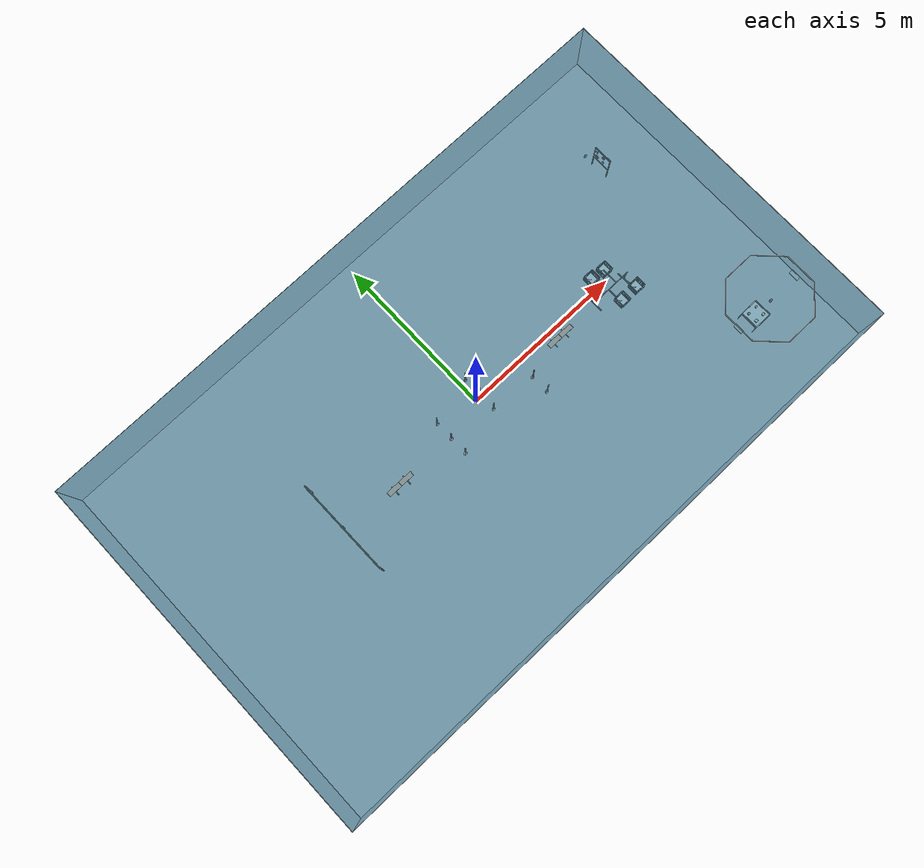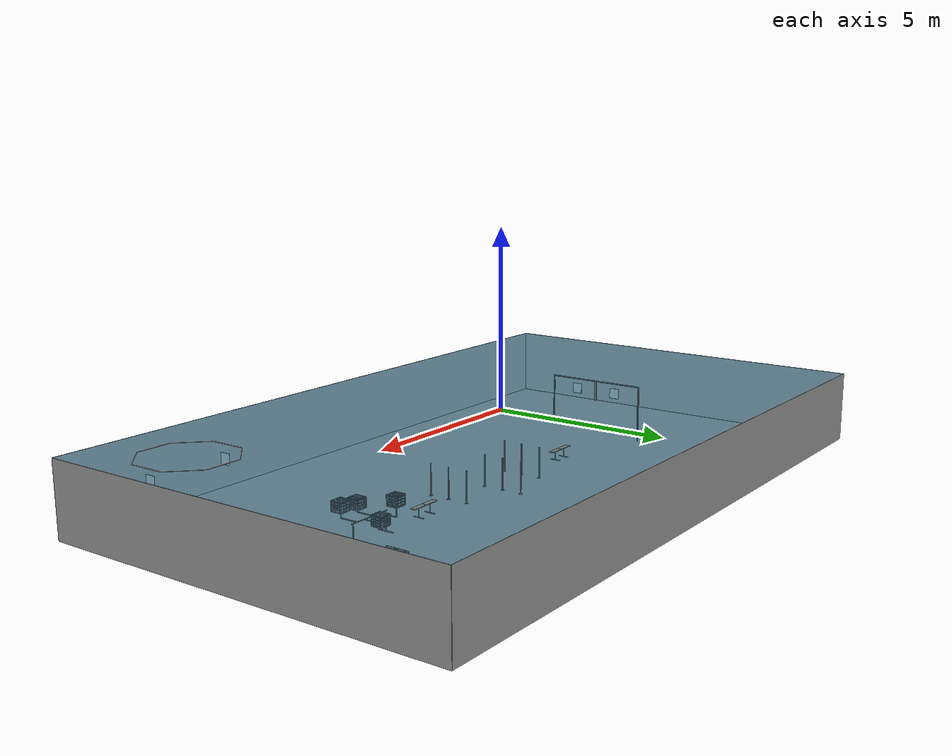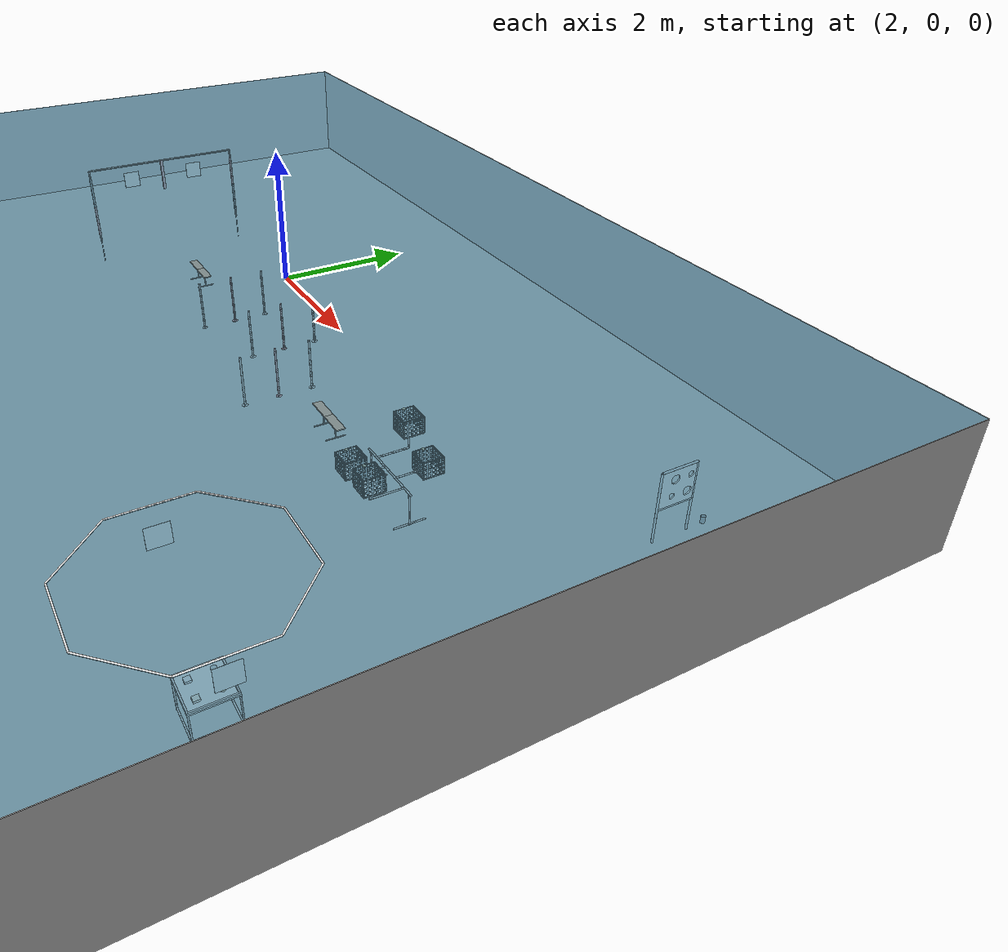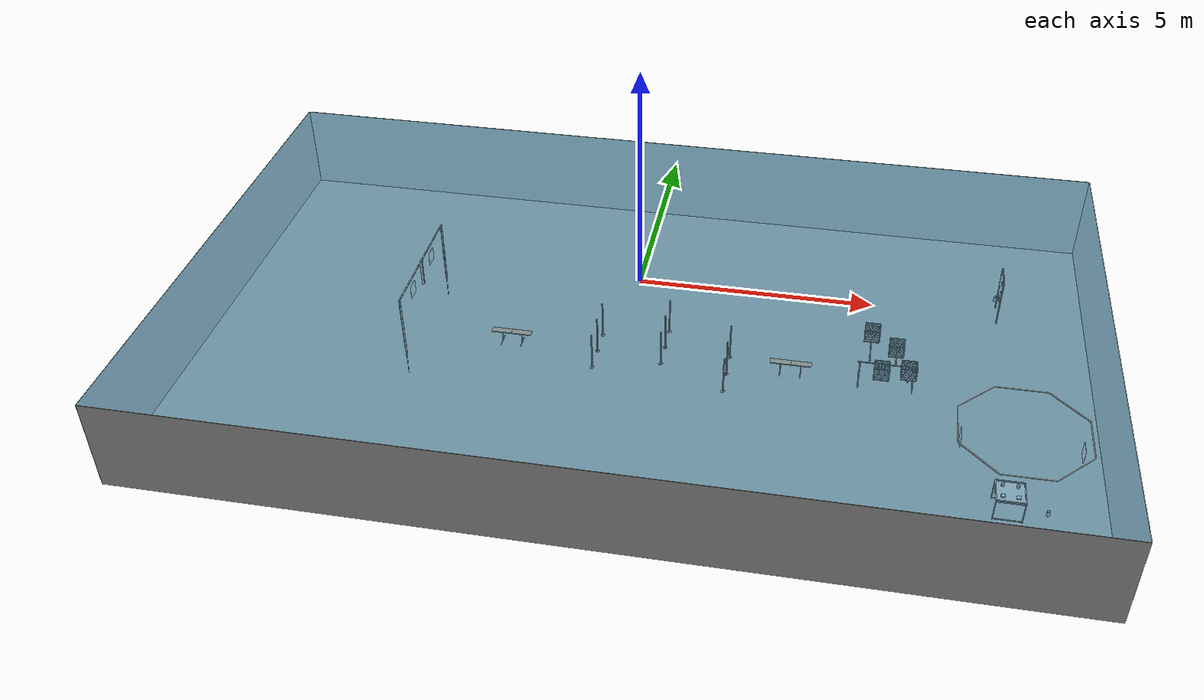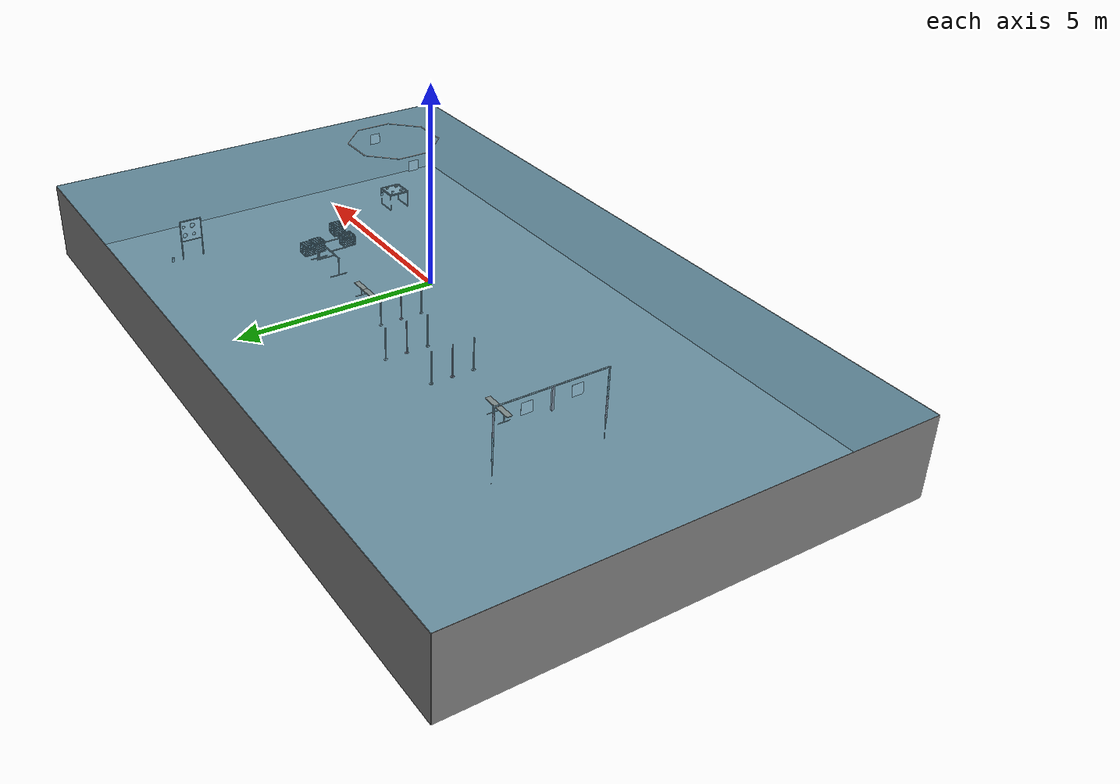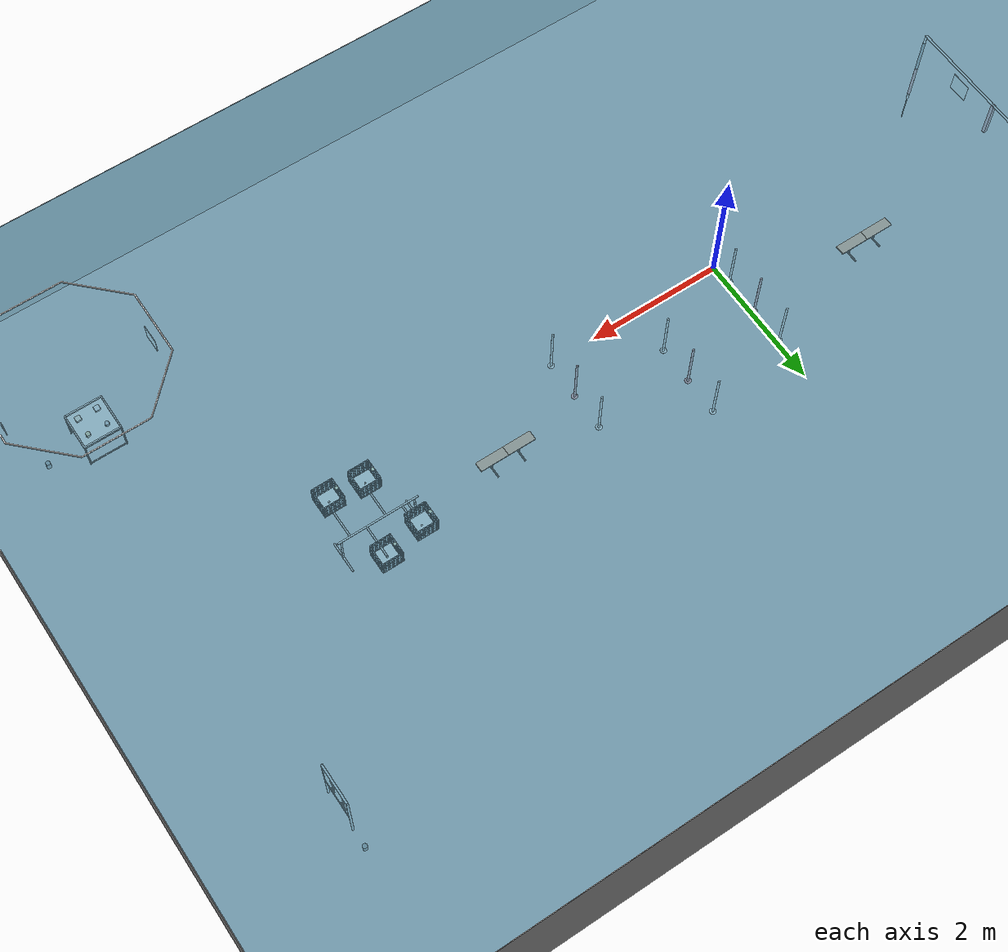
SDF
<sdf version="1.9">
 <world name="robosub26_full">
  <plugin filename="gz-sim-particle-emitter-system" name="gz::sim::systems::ParticleEmitter"/>
  <plugin filename="gz-sim-physics-system" name="gz::sim::systems::Physics"/>
  <plugin filename="gz-sim-user-commands-system" name="gz::sim::systems::UserCommands"/>
  <plugin filename="gz-sim-scene-broadcaster-system" name="gz::sim::systems::SceneBroadcaster"/>
  <plugin filename="gz-sim-apply-link-wrench-system" name="gz::sim::systems::ApplyLinkWrench"/>
  <plugin filename="gz-sim-imu-system" name="gz::sim::systems::Imu"/>
  <plugin filename="gz-sim-sensors-system" name="gz::sim::systems::Sensors">
   <render_engine>ogre2</render_engine>
  </plugin>
  <plugin filename="gz-sim-dvl-system" name="gz::sim::systems::DopplerVelocityLogSystem"/>
  <plugin filename="gz-sim-buoyancy-system" name="gz::sim::systems::Buoyancy">
   <graded_buoyancy>
    <default_density>1000</default_density>
    <density_change><above_depth>0</above_depth><density>1</density></density_change>
   </graded_buoyancy>
   <enable>mongla</enable>
   <enable>gate</enable>
   <enable>slalom_1</enable>
   <enable>slalom_2</enable>
   <enable>slalom_3</enable>
   <enable>item_bolt</enable>
   <enable>item_plug</enable>
   <enable>item_pill</enable>
   <enable>item_bandage</enable>
   <enable>payload_shot_0</enable>
   <enable>payload_shot_1</enable>
   <enable>payload_shot_2</enable>
   <enable>payload_shot_3</enable>
   <enable>payload_shot_4</enable>
   <enable>payload_shot_5</enable>
   <enable>payload_shot_6</enable>
   <enable>payload_shot_7</enable>
   <enable>payload_shot_8</enable>
   <enable>payload_shot_9</enable>
   <enable>payload_shot_10</enable>
   <enable>payload_shot_11</enable>
  </plugin>
  <physics name="default" type="dart">
   <max_step_size>0.001</max_step_size>
   <real_time_factor>1.0</real_time_factor>
   <real_time_update_rate>1000</real_time_update_rate>
   <dart>
    <collision_detector>bullet</collision_detector>
    <solver><solver_type>dantzig</solver_type></solver>
   </dart>
  </physics>
  <gravity>0 0 -9.81</gravity>
  <magnetic_field>3.9e-05 1.1e-06 2.6e-05</magnetic_field>
  <atmosphere type="adiabatic"/>
  <scene>
   <ambient>0.28 0.4 0.48 1</ambient>
   <background>0.08 0.26 0.4 1</background>
   <shadows>true</shadows>
   <fog>
    <color>0.14 0.34 0.42 1</color>
    <type>linear</type>
    <start>1.2</start>
    <end>22.0</end>
    <density>0.028</density>
   </fog>
  </scene>
  <light type="directional" name="sun">
   <pose>0 0 10 0 0 0</pose>
   <diffuse>0.48 0.52 0.56 1</diffuse>
   <specular>0.10 0.10 0.11 1</specular>
   <direction>-0.4 0.15 -0.9</direction>
  </light>
  <light type="directional" name="fill">
   <cast_shadows>false</cast_shadows>
   <pose>0 0 5 0 0 0</pose>
   <diffuse>0.22 0.28 0.34 1</diffuse>
   <specular>0.04 0.05 0.06 1</specular>
   <direction>0.3 -0.2 -1</direction>
  </light>
  <light type="directional" name="caustic_fill">
   <cast_shadows>false</cast_shadows>
   <pose>0 0 3 0 0 0</pose>
   <diffuse>0.12 0.22 0.26 1</diffuse>
   <specular>0.02 0.03 0.04 1</specular>
   <direction>0.1 0.35 -0.85</direction>
  </light>
  <model name="robosub_pool">
   <static>true</static>
   <link name="floor">
    <pose>0 0 -2.1 0 0 0</pose>
    <inertial>
     <mass>1000</mass>
     <inertia><ixx>1000</ixx><ixy>0</ixy><ixz>0</ixz><iyy>1000</iyy><iyz>0</iyz><izz>1000</izz></inertia>
    </inertial>
    <visual name="floor_visual">
     <pose>0 0 0.005 0 0 0</pose>
     <geometry><box><size>20 12 0.01</size></box></geometry>
     <material>
      <ambient>0.55 0.55 0.55 1</ambient>
      <diffuse>0.55 0.55 0.55 1</diffuse>
      <specular>0.08 0.08 0.08 1</specular>
      <emissive>0 0 0 1</emissive>
      <pbr>
       <metal>
        <albedo_map>model://robosub_textures/pool_floor.png</albedo_map>
        <metalness>0.0</metalness>
        <roughness>0.85</roughness>
       </metal>
      </pbr>
     </material>
    </visual>
    <collision name="floor_collision">
     <pose>0 0 -0.05 0 0 0</pose>
     <geometry><box><size>20 12 0.1</size></box></geometry>
    </collision>
   </link>
   <link name="wall_x_pos">
    <inertial>
     <mass>1000</mass>
     <inertia><ixx>1000</ixx><ixy>0</ixy><ixz>0</ixz><iyy>1000</iyy><iyz>0</iyz><izz>1000</izz></inertia>
    </inertial>
    <visual name="wall_x_pos_visual">
     <pose>10 0 -1.05 0 0 0</pose>
     <geometry><box><size>0.01 12 2.1</size></box></geometry>
     <material>
      <ambient>0.55 0.55 0.55 1</ambient>
      <diffuse>0.55 0.55 0.55 1</diffuse>
      <specular>0.08 0.08 0.08 1</specular>
      <emissive>0 0 0 1</emissive>
      <pbr>
       <metal>
        <albedo_map>model://robosub_textures/pool_wall_long.png</albedo_map>
        <metalness>0.0</metalness>
        <roughness>0.85</roughness>
       </metal>
      </pbr>
     </material>
    </visual>
    <collision name="wall_x_pos_collision">
     <pose>10.105 0 -1.05 0 0 0</pose>
     <geometry><box><size>0.2 12.4 2.1</size></box></geometry>
    </collision>
   </link>
   <link name="wall_x_neg">
    <inertial>
     <mass>1000</mass>
     <inertia><ixx>1000</ixx><ixy>0</ixy><ixz>0</ixz><iyy>1000</iyy><iyz>0</iyz><izz>1000</izz></inertia>
    </inertial>
    <visual name="wall_x_neg_visual">
     <pose>-10 0 -1.05 0 0 0</pose>
     <geometry><box><size>0.01 12 2.1</size></box></geometry>
     <material>
      <ambient>0.55 0.55 0.55 1</ambient>
      <diffuse>0.55 0.55 0.55 1</diffuse>
      <specular>0.08 0.08 0.08 1</specular>
      <emissive>0 0 0 1</emissive>
      <pbr>
       <metal>
        <albedo_map>model://robosub_textures/pool_wall_long.png</albedo_map>
        <metalness>0.0</metalness>
        <roughness>0.85</roughness>
       </metal>
      </pbr>
     </material>
    </visual>
    <collision name="wall_x_neg_collision">
     <pose>-10.105 0 -1.05 0 0 0</pose>
     <geometry><box><size>0.2 12.4 2.1</size></box></geometry>
    </collision>
   </link>
   <link name="wall_y_pos">
    <inertial>
     <mass>1000</mass>
     <inertia><ixx>1000</ixx><ixy>0</ixy><ixz>0</ixz><iyy>1000</iyy><iyz>0</iyz><izz>1000</izz></inertia>
    </inertial>
    <visual name="wall_y_pos_visual">
     <pose>0 6 -1.05 0 0 0</pose>
     <geometry><box><size>20 0.01 2.1</size></box></geometry>
     <material>
      <ambient>0.55 0.55 0.55 1</ambient>
      <diffuse>0.55 0.55 0.55 1</diffuse>
      <specular>0.08 0.08 0.08 1</specular>
      <emissive>0 0 0 1</emissive>
      <pbr>
       <metal>
        <albedo_map>model://robosub_textures/pool_wall_short.png</albedo_map>
        <metalness>0.0</metalness>
        <roughness>0.85</roughness>
       </metal>
      </pbr>
     </material>
    </visual>
    <collision name="wall_y_pos_collision">
     <pose>0 6.105 -1.05 0 0 0</pose>
     <geometry><box><size>20 0.2 2.1</size></box></geometry>
    </collision>
   </link>
   <link name="wall_y_neg">
    <inertial>
     <mass>1000</mass>
     <inertia><ixx>1000</ixx><ixy>0</ixy><ixz>0</ixz><iyy>1000</iyy><iyz>0</iyz><izz>1000</izz></inertia>
    </inertial>
    <visual name="wall_y_neg_visual">
     <pose>0 -6 -1.05 0 0 0</pose>
     <geometry><box><size>20 0.01 2.1</size></box></geometry>
     <material>
      <ambient>0.55 0.55 0.55 1</ambient>
      <diffuse>0.55 0.55 0.55 1</diffuse>
      <specular>0.08 0.08 0.08 1</specular>
      <emissive>0 0 0 1</emissive>
      <pbr>
       <metal>
        <albedo_map>model://robosub_textures/pool_wall_short.png</albedo_map>
        <metalness>0.0</metalness>
        <roughness>0.85</roughness>
       </metal>
      </pbr>
     </material>
    </visual>
    <collision name="wall_y_neg_collision">
     <pose>0 -6.105 -1.05 0 0 0</pose>
     <geometry><box><size>20 0.2 2.1</size></box></geometry>
    </collision>
   </link>
   <link name="water_surface">
    <inertial>
     <mass>1</mass>
     <inertia><ixx>1</ixx><ixy>0</ixy><ixz>0</ixz><iyy>1</iyy><iyz>0</iyz><izz>1</izz></inertia>
    </inertial>
    <visual name="water_surface_visual">
     <cast_shadows>false</cast_shadows>
     <transparency>0.18</transparency>
     <geometry><mesh><uri>model://robosub_meshes/meshes/water_robosub.obj</uri></mesh></geometry>
     <material>
      <ambient>0.42 0.6 0.68 1</ambient>
      <diffuse>0.42 0.6 0.68 1</diffuse>
      <specular>0.35 0.35 0.35 1</specular>
      <emissive>0.1 0.1 0.1 1</emissive>
      <pbr>
       <metal>
        <albedo_map>model://robosub_textures/water_surface.png</albedo_map>
        <metalness>0.0</metalness>
        <roughness>0.15</roughness>
       </metal>
      </pbr>
     </material>
    </visual>
   </link>
  </model>
  <model name="marine_snow">
   <static>true</static>
   <pose>0 0 -1.05 0 0 0</pose>
   <link name="link">
    <particle_emitter name="snow" type="box">
     <emitting>true</emitting>
     <size>12 12 2.1</size>
     <particle_size>0.006 0.006 0.006</particle_size>
     <lifetime>30</lifetime>
     <min_velocity>0.004</min_velocity>
     <max_velocity>0.025</max_velocity>
     <scale_rate>0</scale_rate>
     <rate>900</rate>
     <topic>marine_snow</topic>
     <material>
      <diffuse>0.80 0.84 0.80</diffuse>
      <specular>0.05 0.05 0.05</specular>
      <pbr><metal><albedo_map>model://robosub_textures/marine_snow.png</albedo_map></metal></pbr>
     </material>
    </particle_emitter>
   </link>
  </model>
  <include><uri>model://robosub_gate</uri><name>gate</name><pose>-5 0 0 0 0 0</pose></include>
  <include>
   <uri>model://robosub_path_marker</uri>
   <name>path_gate_slalom</name>
   <pose>-3 0 -2.1 0 0 0</pose>
  </include>
  <include><uri>model://robosub_slalom</uri><name>slalom_1</name><pose>-1 0 -2.1 0 0 0</pose></include>
  <include><uri>model://robosub_slalom</uri><name>slalom_2</name><pose>0.5 0.4 -2.1 0 0 0</pose></include>
  <include><uri>model://robosub_slalom</uri><name>slalom_3</name><pose>2 -0.3 -2.1 0 0 0</pose></include>
  <include>
   <uri>model://robosub_path_marker</uri>
   <name>path_slalom_bins</name>
   <pose>3.4 0 -2.1 0 0 0</pose>
  </include>
  <include><uri>model://robosub_bins</uri><name>bins</name><pose>5.5 0 -2.1 0 0 0</pose></include>
  <include>
   <uri>model://robosub_torpedo_survey_repair</uri>
   <name>torpedo_board</name>
   <pose>8 3 -2.1 -0 -0 3.1416</pose>
  </include>
  <include><uri>model://robosub_pinger</uri><name>pinger_deploy</name><pose>8 3.6 -2.1 0 0 0</pose></include>
  <include><uri>model://robosub_octagon</uri><name>octagon</name><pose>8 -3.5 0 0 0 0</pose></include>
  <include>
   <uri>model://robosub_resupply_table</uri>
   <name>resupply_table</name>
   <pose>8 -3.5 -2.1 0 0 0</pose>
  </include>
  <include>
   <uri>model://robosub_pinger</uri>
   <name>pinger_restore</name>
   <pose>8.8 -3.5 -2.1 0 0 0</pose>
  </include>
  <include>
   <uri>model://robosub_item_bolt</uri>
   <name>item_bolt</name>
   <pose>7.85 -3.35 -1.58 0 0 0</pose>
  </include>
  <include>
   <uri>model://robosub_item_plug</uri>
   <name>item_plug</name>
   <pose>8.15 -3.35 -1.58 0 0 0</pose>
  </include>
  <include>
   <uri>model://robosub_item_pill</uri>
   <name>item_pill</name>
   <pose>7.85 -3.65 -1.58 0 0 0</pose>
  </include>
  <include>
   <uri>model://robosub_item_bandage</uri>
   <name>item_bandage</name>
   <pose>8.15 -3.65 -1.58 0 0 0</pose>
  </include>
 </world>
</sdf>

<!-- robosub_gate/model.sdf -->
<sdf version="1.9">
  <model name="robosub_gate">
    <static>false</static>
    <plugin filename="gz-sim-label-system" name="gz::sim::systems::Label">
      <label>12</label>
    </plugin>
    <link name="top_bar">
      <pose>0 0 -0.1 1.5708 0 0</pose>
      <inertial>
        <pose>0 0 0 0 0 0</pose>
        <mass>5</mass>
        <inertia>
          <ixx>3.75035</ixx><ixy>0</ixy><ixz>0</ixz>
          <iyy>3.75035</iyy><iyz>0</iyz>
          <izz>0.000697225</izz>
        </inertia>
      </inertial>
      <visual name="top_bar_visual">
        <pose>0 0 0 0 0 0</pose>
        <geometry><cylinder><radius>0.0167</radius><length>3</length></cylinder></geometry>
        <material>
          <ambient>0.92 0.92 0.92 1</ambient>
          <diffuse>0.92 0.92 0.92 1</diffuse>
          <specular>0.55 0.55 0.55 1</specular>
          <emissive>0.258 0.258 0.258 1</emissive>
          <pbr>
            <metal>
              <albedo_map>model://robosub_textures/albedo_pvc.png</albedo_map>
              <metalness>0.0</metalness>
              <roughness_map>model://robosub_textures/rough_pvc.png</roughness_map>
              <normal_map>model://robosub_textures/norm_pvc.png</normal_map>
            </metal>
          </pbr>
        </material>
      </visual>
      <collision name="top_bar_collision">
        <pose>0 0 0 0 0 0</pose>
        <geometry><cylinder><radius>0.0167</radius><length>3</length></cylinder></geometry>
      </collision>
    </link>
    <link name="post_port">
      <pose>0 -1.5 -0.85 0 0 0</pose>
      <inertial>
        <pose>0 0 0 0 0 0</pose>
        <mass>4</mass>
        <inertia>
          <ixx>0.750279</ixx><ixy>0</ixy><ixz>0</ixz>
          <iyy>0.750279</iyy><iyz>0</iyz>
          <izz>0.00055778</izz>
        </inertia>
      </inertial>
      <visual name="post_port_visual">
        <pose>0 0 0 0 0 0</pose>
        <geometry><cylinder><radius>0.0167</radius><length>1.5</length></cylinder></geometry>
        <material>
          <ambient>0.92 0.92 0.92 1</ambient>
          <diffuse>0.92 0.92 0.92 1</diffuse>
          <specular>0.55 0.55 0.55 1</specular>
          <emissive>0.258 0.258 0.258 1</emissive>
          <pbr>
            <metal>
              <albedo_map>model://robosub_textures/albedo_pvc.png</albedo_map>
              <metalness>0.0</metalness>
              <roughness_map>model://robosub_textures/rough_pvc.png</roughness_map>
              <normal_map>model://robosub_textures/norm_pvc.png</normal_map>
            </metal>
          </pbr>
        </material>
      </visual>
      <collision name="post_port_collision">
        <pose>0 0 0 0 0 0</pose>
        <geometry><cylinder><radius>0.0167</radius><length>1.5</length></cylinder></geometry>
      </collision>
    </link>
    <link name="band_port_upper">
      <pose>0 -1.5 -0.5572 0 0 0</pose>
      <inertial>
        <pose>0 0 0 0 0 0</pose>
        <mass>0.4</mass>
        <inertia>
          <ixx>0.0124306</ixx><ixy>0</ixy><ixz>0</ixz>
          <iyy>0.0124306</iyy><iyz>0</iyz>
          <izz>8.71531e-05</izz>
        </inertia>
      </inertial>
      <visual name="band_port_upper_visual">
        <pose>0 0 0 0 0 0</pose>
        <geometry><cylinder><radius>0.020875</radius><length>0.6096</length></cylinder></geometry>
        <material>
          <ambient>0.07 0.07 0.08 1</ambient>
          <diffuse>0.07 0.07 0.08 1</diffuse>
          <specular>0.2 0.2 0.2 1</specular>
          <emissive>0.0154 0.0154 0.0176 1</emissive>
        </material>
      </visual>
    </link>
    <link name="band_port_lower">
      <pose>0 -1.5 -1.1668 0 0 0</pose>
      <inertial>
        <pose>0 0 0 0 0 0</pose>
        <mass>0.4</mass>
        <inertia>
          <ixx>0.0124306</ixx><ixy>0</ixy><ixz>0</ixz>
          <iyy>0.0124306</iyy><iyz>0</iyz>
          <izz>8.71531e-05</izz>
        </inertia>
      </inertial>
      <visual name="band_port_lower_visual">
        <pose>0 0 0 0 0 0</pose>
        <geometry><cylinder><radius>0.020875</radius><length>0.6096</length></cylinder></geometry>
        <material>
          <ambient>0.72 0.11 0.13 1</ambient>
          <diffuse>0.72 0.11 0.13 1</diffuse>
          <specular>0.2 0.2 0.2 1</specular>
          <emissive>0.1584 0.0242 0.0286 1</emissive>
        </material>
      </visual>
    </link>
    <link name="post_stbd">
      <pose>0 1.5 -0.85 0 0 0</pose>
      <inertial>
        <pose>0 0 0 0 0 0</pose>
        <mass>4</mass>
        <inertia>
          <ixx>0.750279</ixx><ixy>0</ixy><ixz>0</ixz>
          <iyy>0.750279</iyy><iyz>0</iyz>
          <izz>0.00055778</izz>
        </inertia>
      </inertial>
      <visual name="post_stbd_visual">
        <pose>0 0 0 0 0 0</pose>
        <geometry><cylinder><radius>0.0167</radius><length>1.5</length></cylinder></geometry>
        <material>
          <ambient>0.92 0.92 0.92 1</ambient>
          <diffuse>0.92 0.92 0.92 1</diffuse>
          <specular>0.55 0.55 0.55 1</specular>
          <emissive>0.258 0.258 0.258 1</emissive>
          <pbr>
            <metal>
              <albedo_map>model://robosub_textures/albedo_pvc.png</albedo_map>
              <metalness>0.0</metalness>
              <roughness_map>model://robosub_textures/rough_pvc.png</roughness_map>
              <normal_map>model://robosub_textures/norm_pvc.png</normal_map>
            </metal>
          </pbr>
        </material>
      </visual>
      <collision name="post_stbd_collision">
        <pose>0 0 0 0 0 0</pose>
        <geometry><cylinder><radius>0.0167</radius><length>1.5</length></cylinder></geometry>
      </collision>
    </link>
    <link name="band_stbd_upper">
      <pose>0 1.5 -0.5572 0 0 0</pose>
      <inertial>
        <pose>0 0 0 0 0 0</pose>
        <mass>0.4</mass>
        <inertia>
          <ixx>0.0124306</ixx><ixy>0</ixy><ixz>0</ixz>
          <iyy>0.0124306</iyy><iyz>0</iyz>
          <izz>8.71531e-05</izz>
        </inertia>
      </inertial>
      <visual name="band_stbd_upper_visual">
        <pose>0 0 0 0 0 0</pose>
        <geometry><cylinder><radius>0.020875</radius><length>0.6096</length></cylinder></geometry>
        <material>
          <ambient>0.72 0.11 0.13 1</ambient>
          <diffuse>0.72 0.11 0.13 1</diffuse>
          <specular>0.2 0.2 0.2 1</specular>
          <emissive>0.1584 0.0242 0.0286 1</emissive>
        </material>
      </visual>
    </link>
    <link name="band_stbd_lower">
      <pose>0 1.5 -1.1668 0 0 0</pose>
      <inertial>
        <pose>0 0 0 0 0 0</pose>
        <mass>0.4</mass>
        <inertia>
          <ixx>0.0124306</ixx><ixy>0</ixy><ixz>0</ixz>
          <iyy>0.0124306</iyy><iyz>0</iyz>
          <izz>8.71531e-05</izz>
        </inertia>
      </inertial>
      <visual name="band_stbd_lower_visual">
        <pose>0 0 0 0 0 0</pose>
        <geometry><cylinder><radius>0.020875</radius><length>0.6096</length></cylinder></geometry>
        <material>
          <ambient>0.07 0.07 0.08 1</ambient>
          <diffuse>0.07 0.07 0.08 1</diffuse>
          <specular>0.2 0.2 0.2 1</specular>
          <emissive>0.0154 0.0154 0.0176 1</emissive>
        </material>
      </visual>
    </link>
    <link name="divider">
      <pose>0 0 -0.4048 0 0 0</pose>
      <inertial>
        <pose>0 0 0 0 0 0</pose>
        <mass>0.5</mass>
        <inertia>
          <ixx>0.0155914</ixx><ixy>0</ixy><ixz>0</ixz>
          <iyy>0.0155914</iyy><iyz>0</iyz>
          <izz>0.000215053</izz>
        </inertia>
      </inertial>
      <visual name="divider_visual">
        <pose>0 0 0 0 0 0</pose>
        <geometry><box><size>0.0508 0.0508 0.6096</size></box></geometry>
        <material>
          <ambient>0.72 0.11 0.13 1</ambient>
          <diffuse>0.72 0.11 0.13 1</diffuse>
          <specular>0.2 0.2 0.2 1</specular>
          <emissive>0.1584 0.0242 0.0286 1</emissive>
        </material>
      </visual>
      <collision name="divider_collision">
        <pose>0 0 0 0 0 0</pose>
        <geometry><box><size>0.0508 0.0508 0.6096</size></box></geometry>
      </collision>
    </link>
    <link name="sign_survey_repair">
      <pose>0 -0.66 -0.4049 0 0 0</pose>
      <inertial>
        <pose>0 0 0 0 0 0</pose>
        <mass>0.15</mass>
        <inertia>
          <ixx>0.00232562</ixx><ixy>0</ixy><ixz>0</ixz>
          <iyy>0.00116301</iyy><iyz>0</iyz>
          <izz>0.00116301</izz>
        </inertia>
      </inertial>
      <visual name="sign_survey_repair_visual">
        <pose>0 0 0 0 0 0</pose>
        <geometry><box><size>0.004 0.305 0.305</size></box></geometry>
        <material>
          <ambient>1 1 1 1</ambient>
          <diffuse>1 1 1 1</diffuse>
          <specular>0.06 0.06 0.06 1</specular>
          <emissive>0.1 0.1 0.1 1</emissive>
          <pbr>
            <metal>
              <albedo_map>model://robosub_textures/role_compass.png</albedo_map>
              <metalness>0.0</metalness>
              <roughness>0.55</roughness>
            </metal>
          </pbr>
        </material>
      </visual>
      <collision name="sign_survey_repair_collision">
        <pose>0 0 0 0 0 0</pose>
        <geometry><box><size>0.004 0.305 0.305</size></box></geometry>
      </collision>
    </link>
    <link name="sign_search_rescue">
      <pose>0 0.66 -0.4049 0 0 0</pose>
      <inertial>
        <pose>0 0 0 0 0 0</pose>
        <mass>0.15</mass>
        <inertia>
          <ixx>0.00232562</ixx><ixy>0</ixy><ixz>0</ixz>
          <iyy>0.00116301</iyy><iyz>0</iyz>
          <izz>0.00116301</izz>
        </inertia>
      </inertial>
      <visual name="sign_search_rescue_visual">
        <pose>0 0 0 0 0 0</pose>
        <geometry><box><size>0.004 0.305 0.305</size></box></geometry>
        <material>
          <ambient>1 1 1 1</ambient>
          <diffuse>1 1 1 1</diffuse>
          <specular>0.06 0.06 0.06 1</specular>
          <emissive>0.1 0.1 0.1 1</emissive>
          <pbr>
            <metal>
              <albedo_map>model://robosub_textures/role_sos.png</albedo_map>
              <metalness>0.0</metalness>
              <roughness>0.55</roughness>
            </metal>
          </pbr>
        </material>
      </visual>
      <collision name="sign_search_rescue_collision">
        <pose>0 0 0 0 0 0</pose>
        <geometry><box><size>0.004 0.305 0.305</size></box></geometry>
      </collision>
    </link>
    <link name="mooring_port">
      <pose>0 -1.5 -1.85 0 0 0</pose>
      <inertial>
        <pose>0 0 0 0 0 0</pose>
        <mass>0.1</mass>
        <inertia>
          <ixx>0.00208423</ixx><ixy>0</ixy><ixz>0</ixz>
          <iyy>0.00208423</iyy><iyz>0</iyz>
          <izz>1.8e-06</izz>
        </inertia>
      </inertial>
      <visual name="mooring_port_visual">
        <pose>0 0 0 0 0 0</pose>
        <geometry><cylinder><radius>0.006</radius><length>0.5</length></cylinder></geometry>
        <material>
          <ambient>0.15 0.15 0.14 1</ambient>
          <diffuse>0.15 0.15 0.14 1</diffuse>
          <specular>0.2 0.2 0.2 1</specular>
          <emissive>0.0375 0.0375 0.035 1</emissive>
        </material>
      </visual>
    </link>
    <link name="mooring_stbd">
      <pose>0 1.5 -1.85 0 0 0</pose>
      <inertial>
        <pose>0 0 0 0 0 0</pose>
        <mass>0.1</mass>
        <inertia>
          <ixx>0.00208423</ixx><ixy>0</ixy><ixz>0</ixz>
          <iyy>0.00208423</iyy><iyz>0</iyz>
          <izz>1.8e-06</izz>
        </inertia>
      </inertial>
      <visual name="mooring_stbd_visual">
        <pose>0 0 0 0 0 0</pose>
        <geometry><cylinder><radius>0.006</radius><length>0.5</length></cylinder></geometry>
        <material>
          <ambient>0.15 0.15 0.14 1</ambient>
          <diffuse>0.15 0.15 0.14 1</diffuse>
          <specular>0.2 0.2 0.2 1</specular>
          <emissive>0.0375 0.0375 0.035 1</emissive>
        </material>
      </visual>
    </link>
    <joint name="top_bar_post_port_fix" type="fixed">
      <parent>top_bar</parent>
      <child>post_port</child>
    </joint>
    <joint name="top_bar_post_stbd_fix" type="fixed">
      <parent>top_bar</parent>
      <child>post_stbd</child>
    </joint>
    <joint name="top_bar_band_port_upper_fix" type="fixed">
      <parent>top_bar</parent>
      <child>band_port_upper</child>
    </joint>
    <joint name="top_bar_band_port_lower_fix" type="fixed">
      <parent>top_bar</parent>
      <child>band_port_lower</child>
    </joint>
    <joint name="top_bar_band_stbd_upper_fix" type="fixed">
      <parent>top_bar</parent>
      <child>band_stbd_upper</child>
    </joint>
    <joint name="top_bar_band_stbd_lower_fix" type="fixed">
      <parent>top_bar</parent>
      <child>band_stbd_lower</child>
    </joint>
    <joint name="top_bar_mooring_port_fix" type="fixed">
      <parent>top_bar</parent>
      <child>mooring_port</child>
    </joint>
    <joint name="top_bar_mooring_stbd_fix" type="fixed">
      <parent>top_bar</parent>
      <child>mooring_stbd</child>
    </joint>
    <joint name="gate_mooring" type="fixed">
      <parent>world</parent>
      <child>top_bar</child>
    </joint>
    <joint name="sign_survey_repair_hinge" type="revolute">
      <parent>top_bar</parent>
      <child>sign_survey_repair</child>
      <pose>0 0 0.1525 0 0 0</pose>
      <axis>
        <xyz>0 1 0</xyz>
        <limit>
          <lower>-1</lower>
          <upper>1</upper>
        </limit>
        <dynamics>
          <damping>0.4</damping>
          <spring_stiffness>3</spring_stiffness>
          <spring_reference>0</spring_reference>
        </dynamics>
      </axis>
    </joint>
    <plugin filename="gz-sim-hydrodynamics-system" name="gz::sim::systems::Hydrodynamics">
      <link_name>sign_survey_repair</link_name>
      <water_density>1000.0</water_density>
      <xUabsU>-55.815</xUabsU>
      <yVabsV>-55.815</yVabsV>
      <zWabsW>-0.732</zWabsW>
      <kPabsP>-1.29805</kPabsP>
      <mQabsQ>-1.29805</mQabsQ>
      <nRabsR>-1.29805</nRabsR>
    </plugin>
    <joint name="sign_search_rescue_hinge" type="revolute">
      <parent>top_bar</parent>
      <child>sign_search_rescue</child>
      <pose>0 0 0.1525 0 0 0</pose>
      <axis>
        <xyz>0 1 0</xyz>
        <limit>
          <lower>-1</lower>
          <upper>1</upper>
        </limit>
        <dynamics>
          <damping>0.4</damping>
          <spring_stiffness>3</spring_stiffness>
          <spring_reference>0</spring_reference>
        </dynamics>
      </axis>
    </joint>
    <plugin filename="gz-sim-hydrodynamics-system" name="gz::sim::systems::Hydrodynamics">
      <link_name>sign_search_rescue</link_name>
      <water_density>1000.0</water_density>
      <xUabsU>-55.815</xUabsU>
      <yVabsV>-55.815</yVabsV>
      <zWabsW>-0.732</zWabsW>
      <kPabsP>-1.29805</kPabsP>
      <mQabsQ>-1.29805</mQabsQ>
      <nRabsR>-1.29805</nRabsR>
    </plugin>
    <joint name="divider_hinge" type="revolute">
      <parent>top_bar</parent>
      <child>divider</child>
      <pose>0 0 0.3048 0 0 0</pose>
      <axis>
        <xyz>0 1 0</xyz>
        <limit>
          <lower>-1</lower>
          <upper>1</upper>
        </limit>
        <dynamics>
          <damping>0.8</damping>
          <spring_stiffness>6</spring_stiffness>
          <spring_reference>0</spring_reference>
        </dynamics>
      </axis>
    </joint>
    <plugin filename="gz-sim-hydrodynamics-system" name="gz::sim::systems::Hydrodynamics">
      <link_name>divider</link_name>
      <water_density>1000.0</water_density>
      <xUabsU>-222.967</xUabsU>
      <yVabsV>-222.967</yVabsV>
      <zWabsW>-18.5806</zWabsW>
      <kPabsP>-20.7143</kPabsP>
      <mQabsQ>-20.7143</mQabsQ>
      <nRabsR>-20.7143</nRabsR>
    </plugin>
  </model>
</sdf>

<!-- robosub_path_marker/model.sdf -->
<sdf version="1.9">
  <model name="robosub_path_marker">
    <static>true</static>
    <plugin filename="gz-sim-label-system" name="gz::sim::systems::Label">
      <label>19</label>
    </plugin>
    <link name="segment_0">
      <pose>-0.2286 0 0.3 0 0 0</pose>
      <inertial>
        <pose>0 0 0 0 0 0</pose>
        <mass>0.6</mass>
        <inertia>
          <ixx>0.00118129</ixx><ixy>0</ixy><ixz>0</ixz>
          <iyy>0.0104716</iyy><iyz>0</iyz>
          <izz>0.0116129</izz>
        </inertia>
      </inertial>
      <visual name="segment_0_visual">
        <pose>0 0 0 0 0 0</pose>
        <geometry><box><size>0.4572 0.1524 0.02</size></box></geometry>
        <material>
          <ambient>0.95 0.42 0.05 1</ambient>
          <diffuse>0.95 0.42 0.05 1</diffuse>
          <specular>0.2 0.2 0.2 1</specular>
          <emissive>0.304 0.1344 0.016 1</emissive>
        </material>
      </visual>
      <collision name="segment_0_collision">
        <pose>0 0 0 0 0 0</pose>
        <geometry><box><size>0.4572 0.1524 0.02</size></box></geometry>
      </collision>
    </link>
    <link name="stand_0">
      <pose>-0.2286 0 0.15 0 0 0</pose>
      <inertial>
        <pose>0 0 0 0 0 0</pose>
        <mass>0.4</mass>
        <inertia>
          <ixx>0.00301103</ixx><ixy>0</ixy><ixz>0</ixz>
          <iyy>0.00301103</iyy><iyz>0</iyz>
          <izz>2.205e-05</izz>
        </inertia>
      </inertial>
      <visual name="stand_0_visual">
        <pose>0 0 0 0 0 0</pose>
        <geometry><cylinder><radius>0.0105</radius><length>0.3</length></cylinder></geometry>
        <material>
          <ambient>0.92 0.92 0.92 1</ambient>
          <diffuse>0.92 0.92 0.92 1</diffuse>
          <specular>0.55 0.55 0.55 1</specular>
          <emissive>0.258 0.258 0.258 1</emissive>
          <pbr>
            <metal>
              <albedo_map>model://robosub_textures/albedo_pvc.png</albedo_map>
              <metalness>0.0</metalness>
              <roughness_map>model://robosub_textures/rough_pvc.png</roughness_map>
              <normal_map>model://robosub_textures/norm_pvc.png</normal_map>
            </metal>
          </pbr>
        </material>
      </visual>
      <collision name="stand_0_collision">
        <pose>0 0 0 0 0 0</pose>
        <geometry><cylinder><radius>0.0105</radius><length>0.3</length></cylinder></geometry>
      </collision>
    </link>
    <link name="foot_0">
      <pose>-0.2286 0 0.02 1.5708 0 0</pose>
      <inertial>
        <pose>0 0 0 0 0 0</pose>
        <mass>0.4</mass>
        <inertia>
          <ixx>0.00375811</ixx><ixy>0</ixy><ixz>0</ixz>
          <iyy>0.00375811</iyy><iyz>0</iyz>
          <izz>2.205e-05</izz>
        </inertia>
      </inertial>
      <visual name="foot_0_visual">
        <pose>0 0 0 0 0 0</pose>
        <geometry><cylinder><radius>0.0105</radius><length>0.33528</length></cylinder></geometry>
        <material>
          <ambient>0.92 0.92 0.92 1</ambient>
          <diffuse>0.92 0.92 0.92 1</diffuse>
          <specular>0.55 0.55 0.55 1</specular>
          <emissive>0.258 0.258 0.258 1</emissive>
          <pbr>
            <metal>
              <albedo_map>model://robosub_textures/albedo_pvc.png</albedo_map>
              <metalness>0.0</metalness>
              <roughness_map>model://robosub_textures/rough_pvc.png</roughness_map>
              <normal_map>model://robosub_textures/norm_pvc.png</normal_map>
            </metal>
          </pbr>
        </material>
      </visual>
      <collision name="foot_0_collision">
        <pose>0 0 0 0 0 0</pose>
        <geometry><cylinder><radius>0.0105</radius><length>0.33528</length></cylinder></geometry>
      </collision>
    </link>
    <link name="segment_1">
      <pose>0.2286 0 0.3 0 0 0</pose>
      <inertial>
        <pose>0 0 0 0 0 0</pose>
        <mass>0.6</mass>
        <inertia>
          <ixx>0.00118129</ixx><ixy>0</ixy><ixz>0</ixz>
          <iyy>0.0104716</iyy><iyz>0</iyz>
          <izz>0.0116129</izz>
        </inertia>
      </inertial>
      <visual name="segment_1_visual">
        <pose>0 0 0 0 0 0</pose>
        <geometry><box><size>0.4572 0.1524 0.02</size></box></geometry>
        <material>
          <ambient>0.95 0.42 0.05 1</ambient>
          <diffuse>0.95 0.42 0.05 1</diffuse>
          <specular>0.2 0.2 0.2 1</specular>
          <emissive>0.304 0.1344 0.016 1</emissive>
        </material>
      </visual>
      <collision name="segment_1_collision">
        <pose>0 0 0 0 0 0</pose>
        <geometry><box><size>0.4572 0.1524 0.02</size></box></geometry>
      </collision>
    </link>
    <link name="stand_1">
      <pose>0.2286 0 0.15 0 0 0</pose>
      <inertial>
        <pose>0 0 0 0 0 0</pose>
        <mass>0.4</mass>
        <inertia>
          <ixx>0.00301103</ixx><ixy>0</ixy><ixz>0</ixz>
          <iyy>0.00301103</iyy><iyz>0</iyz>
          <izz>2.205e-05</izz>
        </inertia>
      </inertial>
      <visual name="stand_1_visual">
        <pose>0 0 0 0 0 0</pose>
        <geometry><cylinder><radius>0.0105</radius><length>0.3</length></cylinder></geometry>
        <material>
          <ambient>0.92 0.92 0.92 1</ambient>
          <diffuse>0.92 0.92 0.92 1</diffuse>
          <specular>0.55 0.55 0.55 1</specular>
          <emissive>0.258 0.258 0.258 1</emissive>
          <pbr>
            <metal>
              <albedo_map>model://robosub_textures/albedo_pvc.png</albedo_map>
              <metalness>0.0</metalness>
              <roughness_map>model://robosub_textures/rough_pvc.png</roughness_map>
              <normal_map>model://robosub_textures/norm_pvc.png</normal_map>
            </metal>
          </pbr>
        </material>
      </visual>
      <collision name="stand_1_collision">
        <pose>0 0 0 0 0 0</pose>
        <geometry><cylinder><radius>0.0105</radius><length>0.3</length></cylinder></geometry>
      </collision>
    </link>
    <link name="foot_1">
      <pose>0.2286 0 0.02 1.5708 0 0</pose>
      <inertial>
        <pose>0 0 0 0 0 0</pose>
        <mass>0.4</mass>
        <inertia>
          <ixx>0.00375811</ixx><ixy>0</ixy><ixz>0</ixz>
          <iyy>0.00375811</iyy><iyz>0</iyz>
          <izz>2.205e-05</izz>
        </inertia>
      </inertial>
      <visual name="foot_1_visual">
        <pose>0 0 0 0 0 0</pose>
        <geometry><cylinder><radius>0.0105</radius><length>0.33528</length></cylinder></geometry>
        <material>
          <ambient>0.92 0.92 0.92 1</ambient>
          <diffuse>0.92 0.92 0.92 1</diffuse>
          <specular>0.55 0.55 0.55 1</specular>
          <emissive>0.258 0.258 0.258 1</emissive>
          <pbr>
            <metal>
              <albedo_map>model://robosub_textures/albedo_pvc.png</albedo_map>
              <metalness>0.0</metalness>
              <roughness_map>model://robosub_textures/rough_pvc.png</roughness_map>
              <normal_map>model://robosub_textures/norm_pvc.png</normal_map>
            </metal>
          </pbr>
        </material>
      </visual>
      <collision name="foot_1_collision">
        <pose>0 0 0 0 0 0</pose>
        <geometry><cylinder><radius>0.0105</radius><length>0.33528</length></cylinder></geometry>
      </collision>
    </link>
  </model>
</sdf>

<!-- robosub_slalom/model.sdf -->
<sdf version="1.9">
  <model name="robosub_slalom">
    <static>false</static>
    <plugin filename="gz-sim-label-system" name="gz::sim::systems::Label">
      <label>13</label>
    </plugin>
    <link name="pipe_left">
      <pose>0 0.6 0.462 0 0 0</pose>
      <inertial>
        <pose>0 0 0 0 0 0</pose>
        <mass>0.35</mass>
        <inertia>
          <ixx>0.0236494</ixx><ixy>0</ixy><ixz>0</ixz>
          <iyy>0.0236494</iyy><iyz>0</iyz>
          <izz>4.88057e-05</izz>
        </inertia>
      </inertial>
      <visual name="pipe_left_visual">
        <pose>0 0 0 0 0 0</pose>
        <geometry><cylinder><radius>0.0167</radius><length>0.9</length></cylinder></geometry>
        <material>
          <ambient>0.9 0.9 0.9 1</ambient>
          <diffuse>0.9 0.9 0.9 1</diffuse>
          <specular>0.55 0.55 0.55 1</specular>
          <emissive>0.252 0.252 0.252 1</emissive>
          <pbr>
            <metal>
              <albedo_map>model://robosub_textures/albedo_pvc.png</albedo_map>
              <metalness>0.0</metalness>
              <roughness_map>model://robosub_textures/rough_pvc.png</roughness_map>
              <normal_map>model://robosub_textures/norm_pvc.png</normal_map>
            </metal>
          </pbr>
        </material>
      </visual>
      <collision name="pipe_left_collision">
        <pose>0 0 0 0 0 0</pose>
        <geometry><cylinder><radius>0.0167</radius><length>0.9</length></cylinder></geometry>
      </collision>
    </link>
    <link name="pipe_left_anchor">
      <pose>0 0.6 0.006 0 0 0</pose>
      <inertial>
        <pose>0 0 0 0 0 0</pose>
        <mass>0.9</mass>
        <inertia>
          <ixx>0.0005733</ixx><ixy>0</ixy><ixz>0</ixz>
          <iyy>0.0005733</iyy><iyz>0</iyz>
          <izz>0.001125</izz>
        </inertia>
      </inertial>
      <visual name="pipe_left_anchor_visual">
        <pose>0 0 0 0 0 0</pose>
        <geometry><cylinder><radius>0.05</radius><length>0.012</length></cylinder></geometry>
        <material>
          <ambient>0.9 0.9 0.9 1</ambient>
          <diffuse>0.9 0.9 0.9 1</diffuse>
          <specular>0.55 0.55 0.55 1</specular>
          <emissive>0.252 0.252 0.252 1</emissive>
          <pbr>
            <metal>
              <albedo_map>model://robosub_textures/albedo_pvc.png</albedo_map>
              <metalness>0.0</metalness>
              <roughness_map>model://robosub_textures/rough_pvc.png</roughness_map>
              <normal_map>model://robosub_textures/norm_pvc.png</normal_map>
            </metal>
          </pbr>
        </material>
      </visual>
      <collision name="pipe_left_anchor_collision">
        <pose>0 0 0 0 0 0</pose>
        <geometry><cylinder><radius>0.05</radius><length>0.012</length></cylinder></geometry>
        <surface>
          <friction>
            <ode><mu>0.8</mu><mu2>0.8</mu2></ode>
            <bullet><friction>0.8</friction><friction2>0.8</friction2></bullet>
          </friction>
        </surface>
      </collision>
    </link>
    <link name="pipe_centre">
      <pose>0 0 0.462 0 0 0</pose>
      <inertial>
        <pose>0 0 0 0 0 0</pose>
        <mass>0.35</mass>
        <inertia>
          <ixx>0.0236494</ixx><ixy>0</ixy><ixz>0</ixz>
          <iyy>0.0236494</iyy><iyz>0</iyz>
          <izz>4.88057e-05</izz>
        </inertia>
      </inertial>
      <visual name="pipe_centre_visual">
        <pose>0 0 0 0 0 0</pose>
        <geometry><cylinder><radius>0.0167</radius><length>0.9</length></cylinder></geometry>
        <material>
          <ambient>0.72 0.11 0.13 1</ambient>
          <diffuse>0.72 0.11 0.13 1</diffuse>
          <specular>0.55 0.55 0.55 1</specular>
          <emissive>0.202 0.0308 0.0364 1</emissive>
          <pbr>
            <metal>
              <albedo_map>model://robosub_textures/albedo_pvc.png</albedo_map>
              <metalness>0.0</metalness>
              <roughness_map>model://robosub_textures/rough_pvc.png</roughness_map>
              <normal_map>model://robosub_textures/norm_pvc.png</normal_map>
            </metal>
          </pbr>
        </material>
      </visual>
      <collision name="pipe_centre_collision">
        <pose>0 0 0 0 0 0</pose>
        <geometry><cylinder><radius>0.0167</radius><length>0.9</length></cylinder></geometry>
      </collision>
    </link>
    <link name="pipe_centre_anchor">
      <pose>0 0 0.006 0 0 0</pose>
      <inertial>
        <pose>0 0 0 0 0 0</pose>
        <mass>0.9</mass>
        <inertia>
          <ixx>0.0005733</ixx><ixy>0</ixy><ixz>0</ixz>
          <iyy>0.0005733</iyy><iyz>0</iyz>
          <izz>0.001125</izz>
        </inertia>
      </inertial>
      <visual name="pipe_centre_anchor_visual">
        <pose>0 0 0 0 0 0</pose>
        <geometry><cylinder><radius>0.05</radius><length>0.012</length></cylinder></geometry>
        <material>
          <ambient>0.72 0.11 0.13 1</ambient>
          <diffuse>0.72 0.11 0.13 1</diffuse>
          <specular>0.55 0.55 0.55 1</specular>
          <emissive>0.202 0.0308 0.0364 1</emissive>
          <pbr>
            <metal>
              <albedo_map>model://robosub_textures/albedo_pvc.png</albedo_map>
              <metalness>0.0</metalness>
              <roughness_map>model://robosub_textures/rough_pvc.png</roughness_map>
              <normal_map>model://robosub_textures/norm_pvc.png</normal_map>
            </metal>
          </pbr>
        </material>
      </visual>
      <collision name="pipe_centre_anchor_collision">
        <pose>0 0 0 0 0 0</pose>
        <geometry><cylinder><radius>0.05</radius><length>0.012</length></cylinder></geometry>
        <surface>
          <friction>
            <ode><mu>0.8</mu><mu2>0.8</mu2></ode>
            <bullet><friction>0.8</friction><friction2>0.8</friction2></bullet>
          </friction>
        </surface>
      </collision>
    </link>
    <link name="pipe_right">
      <pose>0 -0.6 0.462 0 0 0</pose>
      <inertial>
        <pose>0 0 0 0 0 0</pose>
        <mass>0.35</mass>
        <inertia>
          <ixx>0.0236494</ixx><ixy>0</ixy><ixz>0</ixz>
          <iyy>0.0236494</iyy><iyz>0</iyz>
          <izz>4.88057e-05</izz>
        </inertia>
      </inertial>
      <visual name="pipe_right_visual">
        <pose>0 0 0 0 0 0</pose>
        <geometry><cylinder><radius>0.0167</radius><length>0.9</length></cylinder></geometry>
        <material>
          <ambient>0.9 0.9 0.9 1</ambient>
          <diffuse>0.9 0.9 0.9 1</diffuse>
          <specular>0.55 0.55 0.55 1</specular>
          <emissive>0.252 0.252 0.252 1</emissive>
          <pbr>
            <metal>
              <albedo_map>model://robosub_textures/albedo_pvc.png</albedo_map>
              <metalness>0.0</metalness>
              <roughness_map>model://robosub_textures/rough_pvc.png</roughness_map>
              <normal_map>model://robosub_textures/norm_pvc.png</normal_map>
            </metal>
          </pbr>
        </material>
      </visual>
      <collision name="pipe_right_collision">
        <pose>0 0 0 0 0 0</pose>
        <geometry><cylinder><radius>0.0167</radius><length>0.9</length></cylinder></geometry>
      </collision>
    </link>
    <link name="pipe_right_anchor">
      <pose>0 -0.6 0.006 0 0 0</pose>
      <inertial>
        <pose>0 0 0 0 0 0</pose>
        <mass>0.9</mass>
        <inertia>
          <ixx>0.0005733</ixx><ixy>0</ixy><ixz>0</ixz>
          <iyy>0.0005733</iyy><iyz>0</iyz>
          <izz>0.001125</izz>
        </inertia>
      </inertial>
      <visual name="pipe_right_anchor_visual">
        <pose>0 0 0 0 0 0</pose>
        <geometry><cylinder><radius>0.05</radius><length>0.012</length></cylinder></geometry>
        <material>
          <ambient>0.9 0.9 0.9 1</ambient>
          <diffuse>0.9 0.9 0.9 1</diffuse>
          <specular>0.55 0.55 0.55 1</specular>
          <emissive>0.252 0.252 0.252 1</emissive>
          <pbr>
            <metal>
              <albedo_map>model://robosub_textures/albedo_pvc.png</albedo_map>
              <metalness>0.0</metalness>
              <roughness_map>model://robosub_textures/rough_pvc.png</roughness_map>
              <normal_map>model://robosub_textures/norm_pvc.png</normal_map>
            </metal>
          </pbr>
        </material>
      </visual>
      <collision name="pipe_right_anchor_collision">
        <pose>0 0 0 0 0 0</pose>
        <geometry><cylinder><radius>0.05</radius><length>0.012</length></cylinder></geometry>
        <surface>
          <friction>
            <ode><mu>0.8</mu><mu2>0.8</mu2></ode>
            <bullet><friction>0.8</friction><friction2>0.8</friction2></bullet>
          </friction>
        </surface>
      </collision>
    </link>
    <joint name="pipe_left_mooring" type="fixed">
      <parent>world</parent>
      <child>pipe_left_anchor</child>
    </joint>
    <joint name="pipe_left_hinge" type="universal">
      <parent>pipe_left_anchor</parent>
      <child>pipe_left</child>
      <pose>0 0 -0.45 0 0 0</pose>
      <axis>
        <xyz>1 0 0</xyz>
        <limit>
          <lower>-1.2</lower>
          <upper>1.2</upper>
        </limit>
        <dynamics>
          <damping>0.05</damping>
          <spring_stiffness>0</spring_stiffness>
          <spring_reference>0</spring_reference>
        </dynamics>
      </axis>
      <axis2>
        <xyz>0 1 0</xyz>
        <limit>
          <lower>-1.2</lower>
          <upper>1.2</upper>
        </limit>
        <dynamics>
          <damping>0.05</damping>
          <spring_stiffness>0</spring_stiffness>
          <spring_reference>0</spring_reference>
        </dynamics>
      </axis2>
    </joint>
    <joint name="pipe_centre_mooring" type="fixed">
      <parent>world</parent>
      <child>pipe_centre_anchor</child>
    </joint>
    <joint name="pipe_centre_hinge" type="universal">
      <parent>pipe_centre_anchor</parent>
      <child>pipe_centre</child>
      <pose>0 0 -0.45 0 0 0</pose>
      <axis>
        <xyz>1 0 0</xyz>
        <limit>
          <lower>-1.2</lower>
          <upper>1.2</upper>
        </limit>
        <dynamics>
          <damping>0.05</damping>
          <spring_stiffness>0</spring_stiffness>
          <spring_reference>0</spring_reference>
        </dynamics>
      </axis>
      <axis2>
        <xyz>0 1 0</xyz>
        <limit>
          <lower>-1.2</lower>
          <upper>1.2</upper>
        </limit>
        <dynamics>
          <damping>0.05</damping>
          <spring_stiffness>0</spring_stiffness>
          <spring_reference>0</spring_reference>
        </dynamics>
      </axis2>
    </joint>
    <joint name="pipe_right_mooring" type="fixed">
      <parent>world</parent>
      <child>pipe_right_anchor</child>
    </joint>
    <joint name="pipe_right_hinge" type="universal">
      <parent>pipe_right_anchor</parent>
      <child>pipe_right</child>
      <pose>0 0 -0.45 0 0 0</pose>
      <axis>
        <xyz>1 0 0</xyz>
        <limit>
          <lower>-1.2</lower>
          <upper>1.2</upper>
        </limit>
        <dynamics>
          <damping>0.05</damping>
          <spring_stiffness>0</spring_stiffness>
          <spring_reference>0</spring_reference>
        </dynamics>
      </axis>
      <axis2>
        <xyz>0 1 0</xyz>
        <limit>
          <lower>-1.2</lower>
          <upper>1.2</upper>
        </limit>
        <dynamics>
          <damping>0.05</damping>
          <spring_stiffness>0</spring_stiffness>
          <spring_reference>0</spring_reference>
        </dynamics>
      </axis2>
    </joint>
    <plugin filename="gz-sim-hydrodynamics-system" name="gz::sim::systems::Hydrodynamics">
      <link_name>pipe_left</link_name>
      <water_density>1000.0</water_density>
      <xUabsU>-15.03</xUabsU>
      <yVabsV>-15.03</yVabsV>
      <zWabsW>-0.438079</zWabsW>
      <kPabsP>-2.73922</kPabsP>
      <mQabsQ>-2.73922</mQabsQ>
      <nRabsR>-2.73922</nRabsR>
    </plugin>
    <plugin filename="gz-sim-hydrodynamics-system" name="gz::sim::systems::Hydrodynamics">
      <link_name>pipe_centre</link_name>
      <water_density>1000.0</water_density>
      <xUabsU>-15.03</xUabsU>
      <yVabsV>-15.03</yVabsV>
      <zWabsW>-0.438079</zWabsW>
      <kPabsP>-2.73922</kPabsP>
      <mQabsQ>-2.73922</mQabsQ>
      <nRabsR>-2.73922</nRabsR>
    </plugin>
    <plugin filename="gz-sim-hydrodynamics-system" name="gz::sim::systems::Hydrodynamics">
      <link_name>pipe_right</link_name>
      <water_density>1000.0</water_density>
      <xUabsU>-15.03</xUabsU>
      <yVabsV>-15.03</yVabsV>
      <zWabsW>-0.438079</zWabsW>
      <kPabsP>-2.73922</kPabsP>
      <mQabsQ>-2.73922</mQabsQ>
      <nRabsR>-2.73922</nRabsR>
    </plugin>
  </model>
</sdf>

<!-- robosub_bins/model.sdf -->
<sdf version="1.9">
  <model name="robosub_bins">
    <static>true</static>
    <plugin filename="gz-sim-label-system" name="gz::sim::systems::Label">
      <label>14</label>
    </plugin>
    <link name="spine">
      <pose>0 0 0.55 0 1.5708 0</pose>
      <inertial>
        <pose>0 0 0 0 0 0</pose>
        <mass>1</mass>
        <inertia>
          <ixx>0.140878</ixx><ixy>0</ixy><ixz>0</ixz>
          <iyy>0.140878</iyy><iyz>0</iyz>
          <izz>8.8445e-05</izz>
        </inertia>
      </inertial>
      <visual name="spine_visual">
        <pose>0 0 0 0 0 0</pose>
        <geometry><cylinder><radius>0.0133</radius><length>1.3</length></cylinder></geometry>
        <material>
          <ambient>0.92 0.92 0.92 1</ambient>
          <diffuse>0.92 0.92 0.92 1</diffuse>
          <specular>0.55 0.55 0.55 1</specular>
          <emissive>0.258 0.258 0.258 1</emissive>
          <pbr>
            <metal>
              <albedo_map>model://robosub_textures/albedo_pvc.png</albedo_map>
              <metalness>0.0</metalness>
              <roughness_map>model://robosub_textures/rough_pvc.png</roughness_map>
              <normal_map>model://robosub_textures/norm_pvc.png</normal_map>
            </metal>
          </pbr>
        </material>
      </visual>
      <collision name="spine_collision">
        <pose>0 0 0 0 0 0</pose>
        <geometry><cylinder><radius>0.0133</radius><length>1.3</length></cylinder></geometry>
      </collision>
    </link>
    <link name="foot_riser_0">
      <pose>-0.590909 0 0.275 0 0 0</pose>
      <inertial>
        <pose>0 0 0 0 0 0</pose>
        <mass>1</mass>
        <inertia>
          <ixx>0.0252526</ixx><ixy>0</ixy><ixz>0</ixz>
          <iyy>0.0252526</iyy><iyz>0</iyz>
          <izz>8.8445e-05</izz>
        </inertia>
      </inertial>
      <visual name="foot_riser_0_visual">
        <pose>0 0 0 0 0 0</pose>
        <geometry><cylinder><radius>0.0133</radius><length>0.55</length></cylinder></geometry>
        <material>
          <ambient>0.92 0.92 0.92 1</ambient>
          <diffuse>0.92 0.92 0.92 1</diffuse>
          <specular>0.55 0.55 0.55 1</specular>
          <emissive>0.258 0.258 0.258 1</emissive>
          <pbr>
            <metal>
              <albedo_map>model://robosub_textures/albedo_pvc.png</albedo_map>
              <metalness>0.0</metalness>
              <roughness_map>model://robosub_textures/rough_pvc.png</roughness_map>
              <normal_map>model://robosub_textures/norm_pvc.png</normal_map>
            </metal>
          </pbr>
        </material>
      </visual>
      <collision name="foot_riser_0_collision">
        <pose>0 0 0 0 0 0</pose>
        <geometry><cylinder><radius>0.0133</radius><length>0.55</length></cylinder></geometry>
      </collision>
    </link>
    <link name="foot_0">
      <pose>-0.590909 0 0.03 1.5708 0 0</pose>
      <inertial>
        <pose>0 0 0 0 0 0</pose>
        <mass>1</mass>
        <inertia>
          <ixx>0.0208776</ixx><ixy>0</ixy><ixz>0</ixz>
          <iyy>0.0208776</iyy><iyz>0</iyz>
          <izz>8.8445e-05</izz>
        </inertia>
      </inertial>
      <visual name="foot_0_visual">
        <pose>0 0 0 0 0 0</pose>
        <geometry><cylinder><radius>0.0133</radius><length>0.5</length></cylinder></geometry>
        <material>
          <ambient>0.92 0.92 0.92 1</ambient>
          <diffuse>0.92 0.92 0.92 1</diffuse>
          <specular>0.55 0.55 0.55 1</specular>
          <emissive>0.258 0.258 0.258 1</emissive>
          <pbr>
            <metal>
              <albedo_map>model://robosub_textures/albedo_pvc.png</albedo_map>
              <metalness>0.0</metalness>
              <roughness_map>model://robosub_textures/rough_pvc.png</roughness_map>
              <normal_map>model://robosub_textures/norm_pvc.png</normal_map>
            </metal>
          </pbr>
        </material>
      </visual>
      <collision name="foot_0_collision">
        <pose>0 0 0 0 0 0</pose>
        <geometry><cylinder><radius>0.0133</radius><length>0.5</length></cylinder></geometry>
      </collision>
    </link>
    <link name="foot_riser_1">
      <pose>0.590909 0 0.275 0 0 0</pose>
      <inertial>
        <pose>0 0 0 0 0 0</pose>
        <mass>1</mass>
        <inertia>
          <ixx>0.0252526</ixx><ixy>0</ixy><ixz>0</ixz>
          <iyy>0.0252526</iyy><iyz>0</iyz>
          <izz>8.8445e-05</izz>
        </inertia>
      </inertial>
      <visual name="foot_riser_1_visual">
        <pose>0 0 0 0 0 0</pose>
        <geometry><cylinder><radius>0.0133</radius><length>0.55</length></cylinder></geometry>
        <material>
          <ambient>0.92 0.92 0.92 1</ambient>
          <diffuse>0.92 0.92 0.92 1</diffuse>
          <specular>0.55 0.55 0.55 1</specular>
          <emissive>0.258 0.258 0.258 1</emissive>
          <pbr>
            <metal>
              <albedo_map>model://robosub_textures/albedo_pvc.png</albedo_map>
              <metalness>0.0</metalness>
              <roughness_map>model://robosub_textures/rough_pvc.png</roughness_map>
              <normal_map>model://robosub_textures/norm_pvc.png</normal_map>
            </metal>
          </pbr>
        </material>
      </visual>
      <collision name="foot_riser_1_collision">
        <pose>0 0 0 0 0 0</pose>
        <geometry><cylinder><radius>0.0133</radius><length>0.55</length></cylinder></geometry>
      </collision>
    </link>
    <link name="foot_1">
      <pose>0.590909 0 0.03 1.5708 0 0</pose>
      <inertial>
        <pose>0 0 0 0 0 0</pose>
        <mass>1</mass>
        <inertia>
          <ixx>0.0208776</ixx><ixy>0</ixy><ixz>0</ixz>
          <iyy>0.0208776</iyy><iyz>0</iyz>
          <izz>8.8445e-05</izz>
        </inertia>
      </inertial>
      <visual name="foot_1_visual">
        <pose>0 0 0 0 0 0</pose>
        <geometry><cylinder><radius>0.0133</radius><length>0.5</length></cylinder></geometry>
        <material>
          <ambient>0.92 0.92 0.92 1</ambient>
          <diffuse>0.92 0.92 0.92 1</diffuse>
          <specular>0.55 0.55 0.55 1</specular>
          <emissive>0.258 0.258 0.258 1</emissive>
          <pbr>
            <metal>
              <albedo_map>model://robosub_textures/albedo_pvc.png</albedo_map>
              <metalness>0.0</metalness>
              <roughness_map>model://robosub_textures/rough_pvc.png</roughness_map>
              <normal_map>model://robosub_textures/norm_pvc.png</normal_map>
            </metal>
          </pbr>
        </material>
      </visual>
      <collision name="foot_1_collision">
        <pose>0 0 0 0 0 0</pose>
        <geometry><cylinder><radius>0.0133</radius><length>0.5</length></cylinder></geometry>
      </collision>
    </link>
    <link name="arm_sr_a">
      <pose>-0.39 0.26 0.55 1.5708 0 0</pose>
      <inertial>
        <pose>0 0 0 0 0 0</pose>
        <mass>1</mass>
        <inertia>
          <ixx>0.0225776</ixx><ixy>0</ixy><ixz>0</ixz>
          <iyy>0.0225776</iyy><iyz>0</iyz>
          <izz>8.8445e-05</izz>
        </inertia>
      </inertial>
      <visual name="arm_sr_a_visual">
        <pose>0 0 0 0 0 0</pose>
        <geometry><cylinder><radius>0.0133</radius><length>0.52</length></cylinder></geometry>
        <material>
          <ambient>0.92 0.92 0.92 1</ambient>
          <diffuse>0.92 0.92 0.92 1</diffuse>
          <specular>0.55 0.55 0.55 1</specular>
          <emissive>0.258 0.258 0.258 1</emissive>
          <pbr>
            <metal>
              <albedo_map>model://robosub_textures/albedo_pvc.png</albedo_map>
              <metalness>0.0</metalness>
              <roughness_map>model://robosub_textures/rough_pvc.png</roughness_map>
              <normal_map>model://robosub_textures/norm_pvc.png</normal_map>
            </metal>
          </pbr>
        </material>
      </visual>
      <collision name="arm_sr_a_collision">
        <pose>0 0 0 0 0 0</pose>
        <geometry><cylinder><radius>0.0133</radius><length>0.52</length></cylinder></geometry>
      </collision>
    </link>
    <link name="riser_sr_a">
      <pose>-0.39 0.52 0.7 0 0 0</pose>
      <inertial>
        <pose>0 0 0 0 0 0</pose>
        <mass>1</mass>
        <inertia>
          <ixx>0.00857756</ixx><ixy>0</ixy><ixz>0</ixz>
          <iyy>0.00857756</iyy><iyz>0</iyz>
          <izz>8.8445e-05</izz>
        </inertia>
      </inertial>
      <visual name="riser_sr_a_visual">
        <pose>0 0 0 0 0 0</pose>
        <geometry><cylinder><radius>0.0133</radius><length>0.32</length></cylinder></geometry>
        <material>
          <ambient>0.92 0.92 0.92 1</ambient>
          <diffuse>0.92 0.92 0.92 1</diffuse>
          <specular>0.55 0.55 0.55 1</specular>
          <emissive>0.258 0.258 0.258 1</emissive>
          <pbr>
            <metal>
              <albedo_map>model://robosub_textures/albedo_pvc.png</albedo_map>
              <metalness>0.0</metalness>
              <roughness_map>model://robosub_textures/rough_pvc.png</roughness_map>
              <normal_map>model://robosub_textures/norm_pvc.png</normal_map>
            </metal>
          </pbr>
        </material>
      </visual>
      <collision name="riser_sr_a_collision">
        <pose>0 0 0 0 0 0</pose>
        <geometry><cylinder><radius>0.0133</radius><length>0.32</length></cylinder></geometry>
      </collision>
    </link>
    <link name="crate_sr_a_floor">
      <pose>-0.39 0.52 0.85 0 0 0</pose>
      <inertial>
        <pose>0 0 0 0 0 0</pose>
        <mass>1</mass>
        <inertia>
          <ixx>0.00936408</ixx><ixy>0</ixy><ixz>0</ixz>
          <iyy>0.00936408</iyy><iyz>0</iyz>
          <izz>0.0187042</izz>
        </inertia>
      </inertial>
      <visual name="crate_sr_a_floor_visual">
        <pose>0 0 0 0 0 0</pose>
        <geometry><box><size>0.335 0.335 0.012</size></box></geometry>
        <material>
          <ambient>1 1 1 1</ambient>
          <diffuse>1 1 1 1</diffuse>
          <specular>0.06 0.06 0.06 1</specular>
          <emissive>0.1 0.1 0.1 1</emissive>
          <pbr>
            <metal>
              <albedo_map>model://robosub_textures/role_fire.png</albedo_map>
              <metalness>0.0</metalness>
              <roughness>0.55</roughness>
            </metal>
          </pbr>
        </material>
      </visual>
      <collision name="crate_sr_a_floor_collision">
        <pose>0 0 0 0 0 0</pose>
        <geometry><box><size>0.335 0.335 0.012</size></box></geometry>
      </collision>
    </link>
    <link name="crate_sr_a_xp">
      <pose>-0.2285 0.52 0.99 0 0 0</pose>
      <inertial>
        <pose>0 0 0 0 0 0</pose>
        <mass>0.5</mass>
        <inertia>
          <ixx>0.00794271</ixx><ixy>0</ixy><ixz>0</ixz>
          <iyy>0.00327267</iyy><iyz>0</iyz>
          <izz>0.00468204</izz>
        </inertia>
      </inertial>
      <visual name="crate_sr_a_xp_visual">
        <pose>0 0 0 0 0 0</pose>
        <geometry><mesh><uri>model://robosub_meshes/meshes/crate_wall.obj</uri></mesh></geometry>
        <material>
          <ambient>0.18 0.18 0.2 1</ambient>
          <diffuse>0.18 0.18 0.2 1</diffuse>
          <specular>0.14 0.14 0.14 1</specular>
          <emissive>0.04 0.04 0.04 1</emissive>
          <pbr>
            <metal>
              <albedo_map>model://robosub_textures/albedo_plastic.png</albedo_map>
              <metalness>0.0</metalness>
              <roughness_map>model://robosub_textures/rough_plastic.png</roughness_map>
              <normal_map>model://robosub_textures/norm_plastic.png</normal_map>
              <double_sided>true</double_sided>
            </metal>
          </pbr>
        </material>
      </visual>
      <collision name="crate_sr_a_xp_collision">
        <pose>0 0 0 0 0 0</pose>
        <geometry><box><size>0.012 0.335 0.28</size></box></geometry>
      </collision>
    </link>
    <link name="crate_sr_a_xn">
      <pose>-0.5515 0.52 0.99 0 0 0</pose>
      <inertial>
        <pose>0 0 0 0 0 0</pose>
        <mass>0.5</mass>
        <inertia>
          <ixx>0.00794271</ixx><ixy>0</ixy><ixz>0</ixz>
          <iyy>0.00327267</iyy><iyz>0</iyz>
          <izz>0.00468204</izz>
        </inertia>
      </inertial>
      <visual name="crate_sr_a_xn_visual">
        <pose>0 0 0 0 0 0</pose>
        <geometry><mesh><uri>model://robosub_meshes/meshes/crate_wall.obj</uri></mesh></geometry>
        <material>
          <ambient>0.18 0.18 0.2 1</ambient>
          <diffuse>0.18 0.18 0.2 1</diffuse>
          <specular>0.14 0.14 0.14 1</specular>
          <emissive>0.04 0.04 0.04 1</emissive>
          <pbr>
            <metal>
              <albedo_map>model://robosub_textures/albedo_plastic.png</albedo_map>
              <metalness>0.0</metalness>
              <roughness_map>model://robosub_textures/rough_plastic.png</roughness_map>
              <normal_map>model://robosub_textures/norm_plastic.png</normal_map>
              <double_sided>true</double_sided>
            </metal>
          </pbr>
        </material>
      </visual>
      <collision name="crate_sr_a_xn_collision">
        <pose>0 0 0 0 0 0</pose>
        <geometry><box><size>0.012 0.335 0.28</size></box></geometry>
      </collision>
    </link>
    <link name="crate_sr_a_yp">
      <pose>-0.39 0.6815 0.99 0 0 1.5708</pose>
      <inertial>
        <pose>0 0 0 0 0 0</pose>
        <mass>0.5</mass>
        <inertia>
          <ixx>0.00327267</ixx><ixy>0</ixy><ixz>0</ixz>
          <iyy>0.00794271</iyy><iyz>0</iyz>
          <izz>0.00468204</izz>
        </inertia>
      </inertial>
      <visual name="crate_sr_a_yp_visual">
        <pose>0 0 0 0 0 0</pose>
        <geometry><mesh><uri>model://robosub_meshes/meshes/crate_wall.obj</uri></mesh></geometry>
        <material>
          <ambient>0.18 0.18 0.2 1</ambient>
          <diffuse>0.18 0.18 0.2 1</diffuse>
          <specular>0.14 0.14 0.14 1</specular>
          <emissive>0.04 0.04 0.04 1</emissive>
          <pbr>
            <metal>
              <albedo_map>model://robosub_textures/albedo_plastic.png</albedo_map>
              <metalness>0.0</metalness>
              <roughness_map>model://robosub_textures/rough_plastic.png</roughness_map>
              <normal_map>model://robosub_textures/norm_plastic.png</normal_map>
              <double_sided>true</double_sided>
            </metal>
          </pbr>
        </material>
      </visual>
      <collision name="crate_sr_a_yp_collision">
        <pose>0 0 0 0 0 0</pose>
        <geometry><box><size>0.335 0.012 0.28</size></box></geometry>
      </collision>
    </link>
    <link name="crate_sr_a_yn">
      <pose>-0.39 0.3585 0.99 0 0 1.5708</pose>
      <inertial>
        <pose>0 0 0 0 0 0</pose>
        <mass>0.5</mass>
        <inertia>
          <ixx>0.00327267</ixx><ixy>0</ixy><ixz>0</ixz>
          <iyy>0.00794271</iyy><iyz>0</iyz>
          <izz>0.00468204</izz>
        </inertia>
      </inertial>
      <visual name="crate_sr_a_yn_visual">
        <pose>0 0 0 0 0 0</pose>
        <geometry><mesh><uri>model://robosub_meshes/meshes/crate_wall.obj</uri></mesh></geometry>
        <material>
          <ambient>0.18 0.18 0.2 1</ambient>
          <diffuse>0.18 0.18 0.2 1</diffuse>
          <specular>0.14 0.14 0.14 1</specular>
          <emissive>0.04 0.04 0.04 1</emissive>
          <pbr>
            <metal>
              <albedo_map>model://robosub_textures/albedo_plastic.png</albedo_map>
              <metalness>0.0</metalness>
              <roughness_map>model://robosub_textures/rough_plastic.png</roughness_map>
              <normal_map>model://robosub_textures/norm_plastic.png</normal_map>
              <double_sided>true</double_sided>
            </metal>
          </pbr>
        </material>
      </visual>
      <collision name="crate_sr_a_yn_collision">
        <pose>0 0 0 0 0 0</pose>
        <geometry><box><size>0.335 0.012 0.28</size></box></geometry>
      </collision>
    </link>
    <link name="light_sr_a">
      <pose>-0.5309 0.52 1.13 0 0 0</pose>
      <inertial>
        <pose>0 0 0 0 0 0</pose>
        <mass>0.05</mass>
        <inertia>
          <ixx>8.79883e-06</ixx><ixy>0</ixy><ixz>0</ixz>
          <iyy>8.79883e-06</iyy><iyz>0</iyz>
          <izz>1.59643e-05</izz>
        </inertia>
      </inertial>
      <visual name="light_sr_a_visual">
        <pose>0 0 0 0 0 0</pose>
        <geometry><cylinder><radius>0.02527</radius><length>0.014</length></cylinder></geometry>
        <material>
          <ambient>1 0.92 0.55 1</ambient>
          <diffuse>1 0.92 0.55 1</diffuse>
          <specular>0.2 0.2 0.2 1</specular>
          <emissive>0.85 0.782 0.4675 1</emissive>
        </material>
      </visual>
    </link>
    <link name="arm_rescue_a">
      <pose>-0.13 -0.26 0.55 1.5708 0 0</pose>
      <inertial>
        <pose>0 0 0 0 0 0</pose>
        <mass>1</mass>
        <inertia>
          <ixx>0.0225776</ixx><ixy>0</ixy><ixz>0</ixz>
          <iyy>0.0225776</iyy><iyz>0</iyz>
          <izz>8.8445e-05</izz>
        </inertia>
      </inertial>
      <visual name="arm_rescue_a_visual">
        <pose>0 0 0 0 0 0</pose>
        <geometry><cylinder><radius>0.0133</radius><length>0.52</length></cylinder></geometry>
        <material>
          <ambient>0.92 0.92 0.92 1</ambient>
          <diffuse>0.92 0.92 0.92 1</diffuse>
          <specular>0.55 0.55 0.55 1</specular>
          <emissive>0.258 0.258 0.258 1</emissive>
          <pbr>
            <metal>
              <albedo_map>model://robosub_textures/albedo_pvc.png</albedo_map>
              <metalness>0.0</metalness>
              <roughness_map>model://robosub_textures/rough_pvc.png</roughness_map>
              <normal_map>model://robosub_textures/norm_pvc.png</normal_map>
            </metal>
          </pbr>
        </material>
      </visual>
      <collision name="arm_rescue_a_collision">
        <pose>0 0 0 0 0 0</pose>
        <geometry><cylinder><radius>0.0133</radius><length>0.52</length></cylinder></geometry>
      </collision>
    </link>
    <link name="riser_rescue_a">
      <pose>-0.13 -0.52 0.6 0 0 0</pose>
      <inertial>
        <pose>0 0 0 0 0 0</pose>
        <mass>1</mass>
        <inertia>
          <ixx>0.00124422</ixx><ixy>0</ixy><ixz>0</ixz>
          <iyy>0.00124422</iyy><iyz>0</iyz>
          <izz>8.8445e-05</izz>
        </inertia>
      </inertial>
      <visual name="riser_rescue_a_visual">
        <pose>0 0 0 0 0 0</pose>
        <geometry><cylinder><radius>0.0133</radius><length>0.12</length></cylinder></geometry>
        <material>
          <ambient>0.92 0.92 0.92 1</ambient>
          <diffuse>0.92 0.92 0.92 1</diffuse>
          <specular>0.55 0.55 0.55 1</specular>
          <emissive>0.258 0.258 0.258 1</emissive>
          <pbr>
            <metal>
              <albedo_map>model://robosub_textures/albedo_pvc.png</albedo_map>
              <metalness>0.0</metalness>
              <roughness_map>model://robosub_textures/rough_pvc.png</roughness_map>
              <normal_map>model://robosub_textures/norm_pvc.png</normal_map>
            </metal>
          </pbr>
        </material>
      </visual>
      <collision name="riser_rescue_a_collision">
        <pose>0 0 0 0 0 0</pose>
        <geometry><cylinder><radius>0.0133</radius><length>0.12</length></cylinder></geometry>
      </collision>
    </link>
    <link name="crate_rescue_a_floor">
      <pose>-0.13 -0.52 0.65 0 0 0</pose>
      <inertial>
        <pose>0 0 0 0 0 0</pose>
        <mass>1</mass>
        <inertia>
          <ixx>0.00936408</ixx><ixy>0</ixy><ixz>0</ixz>
          <iyy>0.00936408</iyy><iyz>0</iyz>
          <izz>0.0187042</izz>
        </inertia>
      </inertial>
      <visual name="crate_rescue_a_floor_visual">
        <pose>0 0 0 0 0 0</pose>
        <geometry><box><size>0.335 0.335 0.012</size></box></geometry>
        <material>
          <ambient>1 1 1 1</ambient>
          <diffuse>1 1 1 1</diffuse>
          <specular>0.06 0.06 0.06 1</specular>
          <emissive>0.1 0.1 0.1 1</emissive>
          <pbr>
            <metal>
              <albedo_map>model://robosub_textures/role_droplet.png</albedo_map>
              <metalness>0.0</metalness>
              <roughness>0.55</roughness>
            </metal>
          </pbr>
        </material>
      </visual>
      <collision name="crate_rescue_a_floor_collision">
        <pose>0 0 0 0 0 0</pose>
        <geometry><box><size>0.335 0.335 0.012</size></box></geometry>
      </collision>
    </link>
    <link name="crate_rescue_a_xp">
      <pose>0.0315 -0.52 0.79 0 0 0</pose>
      <inertial>
        <pose>0 0 0 0 0 0</pose>
        <mass>0.5</mass>
        <inertia>
          <ixx>0.00794271</ixx><ixy>0</ixy><ixz>0</ixz>
          <iyy>0.00327267</iyy><iyz>0</iyz>
          <izz>0.00468204</izz>
        </inertia>
      </inertial>
      <visual name="crate_rescue_a_xp_visual">
        <pose>0 0 0 0 0 0</pose>
        <geometry><mesh><uri>model://robosub_meshes/meshes/crate_wall.obj</uri></mesh></geometry>
        <material>
          <ambient>0.18 0.18 0.2 1</ambient>
          <diffuse>0.18 0.18 0.2 1</diffuse>
          <specular>0.14 0.14 0.14 1</specular>
          <emissive>0.04 0.04 0.04 1</emissive>
          <pbr>
            <metal>
              <albedo_map>model://robosub_textures/albedo_plastic.png</albedo_map>
              <metalness>0.0</metalness>
              <roughness_map>model://robosub_textures/rough_plastic.png</roughness_map>
              <normal_map>model://robosub_textures/norm_plastic.png</normal_map>
              <double_sided>true</double_sided>
            </metal>
          </pbr>
        </material>
      </visual>
      <collision name="crate_rescue_a_xp_collision">
        <pose>0 0 0 0 0 0</pose>
        <geometry><box><size>0.012 0.335 0.28</size></box></geometry>
      </collision>
    </link>
    <link name="crate_rescue_a_xn">
      <pose>-0.2915 -0.52 0.79 0 0 0</pose>
      <inertial>
        <pose>0 0 0 0 0 0</pose>
        <mass>0.5</mass>
        <inertia>
          <ixx>0.00794271</ixx><ixy>0</ixy><ixz>0</ixz>
          <iyy>0.00327267</iyy><iyz>0</iyz>
          <izz>0.00468204</izz>
        </inertia>
      </inertial>
      <visual name="crate_rescue_a_xn_visual">
        <pose>0 0 0 0 0 0</pose>
        <geometry><mesh><uri>model://robosub_meshes/meshes/crate_wall.obj</uri></mesh></geometry>
        <material>
          <ambient>0.18 0.18 0.2 1</ambient>
          <diffuse>0.18 0.18 0.2 1</diffuse>
          <specular>0.14 0.14 0.14 1</specular>
          <emissive>0.04 0.04 0.04 1</emissive>
          <pbr>
            <metal>
              <albedo_map>model://robosub_textures/albedo_plastic.png</albedo_map>
              <metalness>0.0</metalness>
              <roughness_map>model://robosub_textures/rough_plastic.png</roughness_map>
              <normal_map>model://robosub_textures/norm_plastic.png</normal_map>
              <double_sided>true</double_sided>
            </metal>
          </pbr>
        </material>
      </visual>
      <collision name="crate_rescue_a_xn_collision">
        <pose>0 0 0 0 0 0</pose>
        <geometry><box><size>0.012 0.335 0.28</size></box></geometry>
      </collision>
    </link>
    <link name="crate_rescue_a_yp">
      <pose>-0.13 -0.3585 0.79 0 0 1.5708</pose>
      <inertial>
        <pose>0 0 0 0 0 0</pose>
        <mass>0.5</mass>
        <inertia>
          <ixx>0.00327267</ixx><ixy>0</ixy><ixz>0</ixz>
          <iyy>0.00794271</iyy><iyz>0</iyz>
          <izz>0.00468204</izz>
        </inertia>
      </inertial>
      <visual name="crate_rescue_a_yp_visual">
        <pose>0 0 0 0 0 0</pose>
        <geometry><mesh><uri>model://robosub_meshes/meshes/crate_wall.obj</uri></mesh></geometry>
        <material>
          <ambient>0.18 0.18 0.2 1</ambient>
          <diffuse>0.18 0.18 0.2 1</diffuse>
          <specular>0.14 0.14 0.14 1</specular>
          <emissive>0.04 0.04 0.04 1</emissive>
          <pbr>
            <metal>
              <albedo_map>model://robosub_textures/albedo_plastic.png</albedo_map>
              <metalness>0.0</metalness>
              <roughness_map>model://robosub_textures/rough_plastic.png</roughness_map>
              <normal_map>model://robosub_textures/norm_plastic.png</normal_map>
              <double_sided>true</double_sided>
            </metal>
          </pbr>
        </material>
      </visual>
      <collision name="crate_rescue_a_yp_collision">
        <pose>0 0 0 0 0 0</pose>
        <geometry><box><size>0.335 0.012 0.28</size></box></geometry>
      </collision>
    </link>
    <link name="crate_rescue_a_yn">
      <pose>-0.13 -0.6815 0.79 0 0 1.5708</pose>
      <inertial>
        <pose>0 0 0 0 0 0</pose>
        <mass>0.5</mass>
        <inertia>
          <ixx>0.00327267</ixx><ixy>0</ixy><ixz>0</ixz>
          <iyy>0.00794271</iyy><iyz>0</iyz>
          <izz>0.00468204</izz>
        </inertia>
      </inertial>
      <visual name="crate_rescue_a_yn_visual">
        <pose>0 0 0 0 0 0</pose>
        <geometry><mesh><uri>model://robosub_meshes/meshes/crate_wall.obj</uri></mesh></geometry>
        <material>
          <ambient>0.18 0.18 0.2 1</ambient>
          <diffuse>0.18 0.18 0.2 1</diffuse>
          <specular>0.14 0.14 0.14 1</specular>
          <emissive>0.04 0.04 0.04 1</emissive>
          <pbr>
            <metal>
              <albedo_map>model://robosub_textures/albedo_plastic.png</albedo_map>
              <metalness>0.0</metalness>
              <roughness_map>model://robosub_textures/rough_plastic.png</roughness_map>
              <normal_map>model://robosub_textures/norm_plastic.png</normal_map>
              <double_sided>true</double_sided>
            </metal>
          </pbr>
        </material>
      </visual>
      <collision name="crate_rescue_a_yn_collision">
        <pose>0 0 0 0 0 0</pose>
        <geometry><box><size>0.335 0.012 0.28</size></box></geometry>
      </collision>
    </link>
    <link name="light_rescue_a">
      <pose>-0.2709 -0.52 0.93 0 0 0</pose>
      <inertial>
        <pose>0 0 0 0 0 0</pose>
        <mass>0.05</mass>
        <inertia>
          <ixx>8.79883e-06</ixx><ixy>0</ixy><ixz>0</ixz>
          <iyy>8.79883e-06</iyy><iyz>0</iyz>
          <izz>1.59643e-05</izz>
        </inertia>
      </inertial>
      <visual name="light_rescue_a_visual">
        <pose>0 0 0 0 0 0</pose>
        <geometry><cylinder><radius>0.02527</radius><length>0.014</length></cylinder></geometry>
        <material>
          <ambient>1 0.92 0.55 1</ambient>
          <diffuse>1 0.92 0.55 1</diffuse>
          <specular>0.2 0.2 0.2 1</specular>
          <emissive>0.85 0.782 0.4675 1</emissive>
        </material>
      </visual>
    </link>
    <link name="arm_sr_b">
      <pose>0.182 0.26 0.55 1.5708 0 0</pose>
      <inertial>
        <pose>0 0 0 0 0 0</pose>
        <mass>1</mass>
        <inertia>
          <ixx>0.0225776</ixx><ixy>0</ixy><ixz>0</ixz>
          <iyy>0.0225776</iyy><iyz>0</iyz>
          <izz>8.8445e-05</izz>
        </inertia>
      </inertial>
      <visual name="arm_sr_b_visual">
        <pose>0 0 0 0 0 0</pose>
        <geometry><cylinder><radius>0.0133</radius><length>0.52</length></cylinder></geometry>
        <material>
          <ambient>0.92 0.92 0.92 1</ambient>
          <diffuse>0.92 0.92 0.92 1</diffuse>
          <specular>0.55 0.55 0.55 1</specular>
          <emissive>0.258 0.258 0.258 1</emissive>
          <pbr>
            <metal>
              <albedo_map>model://robosub_textures/albedo_pvc.png</albedo_map>
              <metalness>0.0</metalness>
              <roughness_map>model://robosub_textures/rough_pvc.png</roughness_map>
              <normal_map>model://robosub_textures/norm_pvc.png</normal_map>
            </metal>
          </pbr>
        </material>
      </visual>
      <collision name="arm_sr_b_collision">
        <pose>0 0 0 0 0 0</pose>
        <geometry><cylinder><radius>0.0133</radius><length>0.52</length></cylinder></geometry>
      </collision>
    </link>
    <link name="riser_sr_b">
      <pose>0.182 0.52 0.525 0 0 0</pose>
      <inertial>
        <pose>0 0 0 0 0 0</pose>
        <mass>1</mass>
        <inertia>
          <ixx>0.000452556</ixx><ixy>0</ixy><ixz>0</ixz>
          <iyy>0.000452556</iyy><iyz>0</iyz>
          <izz>8.8445e-05</izz>
        </inertia>
      </inertial>
      <visual name="riser_sr_b_visual">
        <pose>0 0 0 0 0 0</pose>
        <geometry><cylinder><radius>0.0133</radius><length>0.07</length></cylinder></geometry>
        <material>
          <ambient>0.92 0.92 0.92 1</ambient>
          <diffuse>0.92 0.92 0.92 1</diffuse>
          <specular>0.55 0.55 0.55 1</specular>
          <emissive>0.258 0.258 0.258 1</emissive>
          <pbr>
            <metal>
              <albedo_map>model://robosub_textures/albedo_pvc.png</albedo_map>
              <metalness>0.0</metalness>
              <roughness_map>model://robosub_textures/rough_pvc.png</roughness_map>
              <normal_map>model://robosub_textures/norm_pvc.png</normal_map>
            </metal>
          </pbr>
        </material>
      </visual>
      <collision name="riser_sr_b_collision">
        <pose>0 0 0 0 0 0</pose>
        <geometry><cylinder><radius>0.0133</radius><length>0.07</length></cylinder></geometry>
      </collision>
    </link>
    <link name="crate_sr_b_floor">
      <pose>0.182 0.52 0.5 0 0 0</pose>
      <inertial>
        <pose>0 0 0 0 0 0</pose>
        <mass>1</mass>
        <inertia>
          <ixx>0.00936408</ixx><ixy>0</ixy><ixz>0</ixz>
          <iyy>0.00936408</iyy><iyz>0</iyz>
          <izz>0.0187042</izz>
        </inertia>
      </inertial>
      <visual name="crate_sr_b_floor_visual">
        <pose>0 0 0 0 0 0</pose>
        <geometry><box><size>0.335 0.335 0.012</size></box></geometry>
        <material>
          <ambient>1 1 1 1</ambient>
          <diffuse>1 1 1 1</diffuse>
          <specular>0.06 0.06 0.06 1</specular>
          <emissive>0.1 0.1 0.1 1</emissive>
          <pbr>
            <metal>
              <albedo_map>model://robosub_textures/role_fire.png</albedo_map>
              <metalness>0.0</metalness>
              <roughness>0.55</roughness>
            </metal>
          </pbr>
        </material>
      </visual>
      <collision name="crate_sr_b_floor_collision">
        <pose>0 0 0 0 0 0</pose>
        <geometry><box><size>0.335 0.335 0.012</size></box></geometry>
      </collision>
    </link>
    <link name="crate_sr_b_xp">
      <pose>0.3435 0.52 0.64 0 0 0</pose>
      <inertial>
        <pose>0 0 0 0 0 0</pose>
        <mass>0.5</mass>
        <inertia>
          <ixx>0.00794271</ixx><ixy>0</ixy><ixz>0</ixz>
          <iyy>0.00327267</iyy><iyz>0</iyz>
          <izz>0.00468204</izz>
        </inertia>
      </inertial>
      <visual name="crate_sr_b_xp_visual">
        <pose>0 0 0 0 0 0</pose>
        <geometry><mesh><uri>model://robosub_meshes/meshes/crate_wall.obj</uri></mesh></geometry>
        <material>
          <ambient>0.18 0.18 0.2 1</ambient>
          <diffuse>0.18 0.18 0.2 1</diffuse>
          <specular>0.14 0.14 0.14 1</specular>
          <emissive>0.04 0.04 0.04 1</emissive>
          <pbr>
            <metal>
              <albedo_map>model://robosub_textures/albedo_plastic.png</albedo_map>
              <metalness>0.0</metalness>
              <roughness_map>model://robosub_textures/rough_plastic.png</roughness_map>
              <normal_map>model://robosub_textures/norm_plastic.png</normal_map>
              <double_sided>true</double_sided>
            </metal>
          </pbr>
        </material>
      </visual>
      <collision name="crate_sr_b_xp_collision">
        <pose>0 0 0 0 0 0</pose>
        <geometry><box><size>0.012 0.335 0.28</size></box></geometry>
      </collision>
    </link>
    <link name="crate_sr_b_xn">
      <pose>0.0205 0.52 0.64 0 0 0</pose>
      <inertial>
        <pose>0 0 0 0 0 0</pose>
        <mass>0.5</mass>
        <inertia>
          <ixx>0.00794271</ixx><ixy>0</ixy><ixz>0</ixz>
          <iyy>0.00327267</iyy><iyz>0</iyz>
          <izz>0.00468204</izz>
        </inertia>
      </inertial>
      <visual name="crate_sr_b_xn_visual">
        <pose>0 0 0 0 0 0</pose>
        <geometry><mesh><uri>model://robosub_meshes/meshes/crate_wall.obj</uri></mesh></geometry>
        <material>
          <ambient>0.18 0.18 0.2 1</ambient>
          <diffuse>0.18 0.18 0.2 1</diffuse>
          <specular>0.14 0.14 0.14 1</specular>
          <emissive>0.04 0.04 0.04 1</emissive>
          <pbr>
            <metal>
              <albedo_map>model://robosub_textures/albedo_plastic.png</albedo_map>
              <metalness>0.0</metalness>
              <roughness_map>model://robosub_textures/rough_plastic.png</roughness_map>
              <normal_map>model://robosub_textures/norm_plastic.png</normal_map>
              <double_sided>true</double_sided>
            </metal>
          </pbr>
        </material>
      </visual>
      <collision name="crate_sr_b_xn_collision">
        <pose>0 0 0 0 0 0</pose>
        <geometry><box><size>0.012 0.335 0.28</size></box></geometry>
      </collision>
    </link>
    <link name="crate_sr_b_yp">
      <pose>0.182 0.6815 0.64 0 0 1.5708</pose>
      <inertial>
        <pose>0 0 0 0 0 0</pose>
        <mass>0.5</mass>
        <inertia>
          <ixx>0.00327267</ixx><ixy>0</ixy><ixz>0</ixz>
          <iyy>0.00794271</iyy><iyz>0</iyz>
          <izz>0.00468204</izz>
        </inertia>
      </inertial>
      <visual name="crate_sr_b_yp_visual">
        <pose>0 0 0 0 0 0</pose>
        <geometry><mesh><uri>model://robosub_meshes/meshes/crate_wall.obj</uri></mesh></geometry>
        <material>
          <ambient>0.18 0.18 0.2 1</ambient>
          <diffuse>0.18 0.18 0.2 1</diffuse>
          <specular>0.14 0.14 0.14 1</specular>
          <emissive>0.04 0.04 0.04 1</emissive>
          <pbr>
            <metal>
              <albedo_map>model://robosub_textures/albedo_plastic.png</albedo_map>
              <metalness>0.0</metalness>
              <roughness_map>model://robosub_textures/rough_plastic.png</roughness_map>
              <normal_map>model://robosub_textures/norm_plastic.png</normal_map>
              <double_sided>true</double_sided>
            </metal>
          </pbr>
        </material>
      </visual>
      <collision name="crate_sr_b_yp_collision">
        <pose>0 0 0 0 0 0</pose>
        <geometry><box><size>0.335 0.012 0.28</size></box></geometry>
      </collision>
    </link>
    <link name="crate_sr_b_yn">
      <pose>0.182 0.3585 0.64 0 0 1.5708</pose>
      <inertial>
        <pose>0 0 0 0 0 0</pose>
        <mass>0.5</mass>
        <inertia>
          <ixx>0.00327267</ixx><ixy>0</ixy><ixz>0</ixz>
          <iyy>0.00794271</iyy><iyz>0</iyz>
          <izz>0.00468204</izz>
        </inertia>
      </inertial>
      <visual name="crate_sr_b_yn_visual">
        <pose>0 0 0 0 0 0</pose>
        <geometry><mesh><uri>model://robosub_meshes/meshes/crate_wall.obj</uri></mesh></geometry>
        <material>
          <ambient>0.18 0.18 0.2 1</ambient>
          <diffuse>0.18 0.18 0.2 1</diffuse>
          <specular>0.14 0.14 0.14 1</specular>
          <emissive>0.04 0.04 0.04 1</emissive>
          <pbr>
            <metal>
              <albedo_map>model://robosub_textures/albedo_plastic.png</albedo_map>
              <metalness>0.0</metalness>
              <roughness_map>model://robosub_textures/rough_plastic.png</roughness_map>
              <normal_map>model://robosub_textures/norm_plastic.png</normal_map>
              <double_sided>true</double_sided>
            </metal>
          </pbr>
        </material>
      </visual>
      <collision name="crate_sr_b_yn_collision">
        <pose>0 0 0 0 0 0</pose>
        <geometry><box><size>0.335 0.012 0.28</size></box></geometry>
      </collision>
    </link>
    <link name="light_sr_b">
      <pose>0.0411 0.52 0.78 0 0 0</pose>
      <inertial>
        <pose>0 0 0 0 0 0</pose>
        <mass>0.05</mass>
        <inertia>
          <ixx>8.79883e-06</ixx><ixy>0</ixy><ixz>0</ixz>
          <iyy>8.79883e-06</iyy><iyz>0</iyz>
          <izz>1.59643e-05</izz>
        </inertia>
      </inertial>
      <visual name="light_sr_b_visual">
        <pose>0 0 0 0 0 0</pose>
        <geometry><cylinder><radius>0.02527</radius><length>0.014</length></cylinder></geometry>
        <material>
          <ambient>1 0.92 0.55 1</ambient>
          <diffuse>1 0.92 0.55 1</diffuse>
          <specular>0.2 0.2 0.2 1</specular>
          <emissive>0.85 0.782 0.4675 1</emissive>
        </material>
      </visual>
    </link>
    <link name="arm_rescue_b">
      <pose>0.442 -0.26 0.55 1.5708 0 0</pose>
      <inertial>
        <pose>0 0 0 0 0 0</pose>
        <mass>1</mass>
        <inertia>
          <ixx>0.0225776</ixx><ixy>0</ixy><ixz>0</ixz>
          <iyy>0.0225776</iyy><iyz>0</iyz>
          <izz>8.8445e-05</izz>
        </inertia>
      </inertial>
      <visual name="arm_rescue_b_visual">
        <pose>0 0 0 0 0 0</pose>
        <geometry><cylinder><radius>0.0133</radius><length>0.52</length></cylinder></geometry>
        <material>
          <ambient>0.92 0.92 0.92 1</ambient>
          <diffuse>0.92 0.92 0.92 1</diffuse>
          <specular>0.55 0.55 0.55 1</specular>
          <emissive>0.258 0.258 0.258 1</emissive>
          <pbr>
            <metal>
              <albedo_map>model://robosub_textures/albedo_pvc.png</albedo_map>
              <metalness>0.0</metalness>
              <roughness_map>model://robosub_textures/rough_pvc.png</roughness_map>
              <normal_map>model://robosub_textures/norm_pvc.png</normal_map>
            </metal>
          </pbr>
        </material>
      </visual>
      <collision name="arm_rescue_b_collision">
        <pose>0 0 0 0 0 0</pose>
        <geometry><cylinder><radius>0.0133</radius><length>0.52</length></cylinder></geometry>
      </collision>
    </link>
    <link name="riser_rescue_b">
      <pose>0.442 -0.52 0.64 0 0 0</pose>
      <inertial>
        <pose>0 0 0 0 0 0</pose>
        <mass>1</mass>
        <inertia>
          <ixx>0.00337756</ixx><ixy>0</ixy><ixz>0</ixz>
          <iyy>0.00337756</iyy><iyz>0</iyz>
          <izz>8.8445e-05</izz>
        </inertia>
      </inertial>
      <visual name="riser_rescue_b_visual">
        <pose>0 0 0 0 0 0</pose>
        <geometry><cylinder><radius>0.0133</radius><length>0.2</length></cylinder></geometry>
        <material>
          <ambient>0.92 0.92 0.92 1</ambient>
          <diffuse>0.92 0.92 0.92 1</diffuse>
          <specular>0.55 0.55 0.55 1</specular>
          <emissive>0.258 0.258 0.258 1</emissive>
          <pbr>
            <metal>
              <albedo_map>model://robosub_textures/albedo_pvc.png</albedo_map>
              <metalness>0.0</metalness>
              <roughness_map>model://robosub_textures/rough_pvc.png</roughness_map>
              <normal_map>model://robosub_textures/norm_pvc.png</normal_map>
            </metal>
          </pbr>
        </material>
      </visual>
      <collision name="riser_rescue_b_collision">
        <pose>0 0 0 0 0 0</pose>
        <geometry><cylinder><radius>0.0133</radius><length>0.2</length></cylinder></geometry>
      </collision>
    </link>
    <link name="crate_rescue_b_floor">
      <pose>0.442 -0.52 0.73 0 0 0</pose>
      <inertial>
        <pose>0 0 0 0 0 0</pose>
        <mass>1</mass>
        <inertia>
          <ixx>0.00936408</ixx><ixy>0</ixy><ixz>0</ixz>
          <iyy>0.00936408</iyy><iyz>0</iyz>
          <izz>0.0187042</izz>
        </inertia>
      </inertial>
      <visual name="crate_rescue_b_floor_visual">
        <pose>0 0 0 0 0 0</pose>
        <geometry><box><size>0.335 0.335 0.012</size></box></geometry>
        <material>
          <ambient>1 1 1 1</ambient>
          <diffuse>1 1 1 1</diffuse>
          <specular>0.06 0.06 0.06 1</specular>
          <emissive>0.1 0.1 0.1 1</emissive>
          <pbr>
            <metal>
              <albedo_map>model://robosub_textures/role_droplet.png</albedo_map>
              <metalness>0.0</metalness>
              <roughness>0.55</roughness>
            </metal>
          </pbr>
        </material>
      </visual>
      <collision name="crate_rescue_b_floor_collision">
        <pose>0 0 0 0 0 0</pose>
        <geometry><box><size>0.335 0.335 0.012</size></box></geometry>
      </collision>
    </link>
    <link name="crate_rescue_b_xp">
      <pose>0.6035 -0.52 0.87 0 0 0</pose>
      <inertial>
        <pose>0 0 0 0 0 0</pose>
        <mass>0.5</mass>
        <inertia>
          <ixx>0.00794271</ixx><ixy>0</ixy><ixz>0</ixz>
          <iyy>0.00327267</iyy><iyz>0</iyz>
          <izz>0.00468204</izz>
        </inertia>
      </inertial>
      <visual name="crate_rescue_b_xp_visual">
        <pose>0 0 0 0 0 0</pose>
        <geometry><mesh><uri>model://robosub_meshes/meshes/crate_wall.obj</uri></mesh></geometry>
        <material>
          <ambient>0.18 0.18 0.2 1</ambient>
          <diffuse>0.18 0.18 0.2 1</diffuse>
          <specular>0.14 0.14 0.14 1</specular>
          <emissive>0.04 0.04 0.04 1</emissive>
          <pbr>
            <metal>
              <albedo_map>model://robosub_textures/albedo_plastic.png</albedo_map>
              <metalness>0.0</metalness>
              <roughness_map>model://robosub_textures/rough_plastic.png</roughness_map>
              <normal_map>model://robosub_textures/norm_plastic.png</normal_map>
              <double_sided>true</double_sided>
            </metal>
          </pbr>
        </material>
      </visual>
      <collision name="crate_rescue_b_xp_collision">
        <pose>0 0 0 0 0 0</pose>
        <geometry><box><size>0.012 0.335 0.28</size></box></geometry>
      </collision>
    </link>
    <link name="crate_rescue_b_xn">
      <pose>0.2805 -0.52 0.87 0 0 0</pose>
      <inertial>
        <pose>0 0 0 0 0 0</pose>
        <mass>0.5</mass>
        <inertia>
          <ixx>0.00794271</ixx><ixy>0</ixy><ixz>0</ixz>
          <iyy>0.00327267</iyy><iyz>0</iyz>
          <izz>0.00468204</izz>
        </inertia>
      </inertial>
      <visual name="crate_rescue_b_xn_visual">
        <pose>0 0 0 0 0 0</pose>
        <geometry><mesh><uri>model://robosub_meshes/meshes/crate_wall.obj</uri></mesh></geometry>
        <material>
          <ambient>0.18 0.18 0.2 1</ambient>
          <diffuse>0.18 0.18 0.2 1</diffuse>
          <specular>0.14 0.14 0.14 1</specular>
          <emissive>0.04 0.04 0.04 1</emissive>
          <pbr>
            <metal>
              <albedo_map>model://robosub_textures/albedo_plastic.png</albedo_map>
              <metalness>0.0</metalness>
              <roughness_map>model://robosub_textures/rough_plastic.png</roughness_map>
              <normal_map>model://robosub_textures/norm_plastic.png</normal_map>
              <double_sided>true</double_sided>
            </metal>
          </pbr>
        </material>
      </visual>
      <collision name="crate_rescue_b_xn_collision">
        <pose>0 0 0 0 0 0</pose>
        <geometry><box><size>0.012 0.335 0.28</size></box></geometry>
      </collision>
    </link>
    <link name="crate_rescue_b_yp">
      <pose>0.442 -0.3585 0.87 0 0 1.5708</pose>
      <inertial>
        <pose>0 0 0 0 0 0</pose>
        <mass>0.5</mass>
        <inertia>
          <ixx>0.00327267</ixx><ixy>0</ixy><ixz>0</ixz>
          <iyy>0.00794271</iyy><iyz>0</iyz>
          <izz>0.00468204</izz>
        </inertia>
      </inertial>
      <visual name="crate_rescue_b_yp_visual">
        <pose>0 0 0 0 0 0</pose>
        <geometry><mesh><uri>model://robosub_meshes/meshes/crate_wall.obj</uri></mesh></geometry>
        <material>
          <ambient>0.18 0.18 0.2 1</ambient>
          <diffuse>0.18 0.18 0.2 1</diffuse>
          <specular>0.14 0.14 0.14 1</specular>
          <emissive>0.04 0.04 0.04 1</emissive>
          <pbr>
            <metal>
              <albedo_map>model://robosub_textures/albedo_plastic.png</albedo_map>
              <metalness>0.0</metalness>
              <roughness_map>model://robosub_textures/rough_plastic.png</roughness_map>
              <normal_map>model://robosub_textures/norm_plastic.png</normal_map>
              <double_sided>true</double_sided>
            </metal>
          </pbr>
        </material>
      </visual>
      <collision name="crate_rescue_b_yp_collision">
        <pose>0 0 0 0 0 0</pose>
        <geometry><box><size>0.335 0.012 0.28</size></box></geometry>
      </collision>
    </link>
    <link name="crate_rescue_b_yn">
      <pose>0.442 -0.6815 0.87 0 0 1.5708</pose>
      <inertial>
        <pose>0 0 0 0 0 0</pose>
        <mass>0.5</mass>
        <inertia>
          <ixx>0.00327267</ixx><ixy>0</ixy><ixz>0</ixz>
          <iyy>0.00794271</iyy><iyz>0</iyz>
          <izz>0.00468204</izz>
        </inertia>
      </inertial>
      <visual name="crate_rescue_b_yn_visual">
        <pose>0 0 0 0 0 0</pose>
        <geometry><mesh><uri>model://robosub_meshes/meshes/crate_wall.obj</uri></mesh></geometry>
        <material>
          <ambient>0.18 0.18 0.2 1</ambient>
          <diffuse>0.18 0.18 0.2 1</diffuse>
          <specular>0.14 0.14 0.14 1</specular>
          <emissive>0.04 0.04 0.04 1</emissive>
          <pbr>
            <metal>
              <albedo_map>model://robosub_textures/albedo_plastic.png</albedo_map>
              <metalness>0.0</metalness>
              <roughness_map>model://robosub_textures/rough_plastic.png</roughness_map>
              <normal_map>model://robosub_textures/norm_plastic.png</normal_map>
              <double_sided>true</double_sided>
            </metal>
          </pbr>
        </material>
      </visual>
      <collision name="crate_rescue_b_yn_collision">
        <pose>0 0 0 0 0 0</pose>
        <geometry><box><size>0.335 0.012 0.28</size></box></geometry>
      </collision>
    </link>
    <link name="light_rescue_b">
      <pose>0.3011 -0.52 1.01 0 0 0</pose>
      <inertial>
        <pose>0 0 0 0 0 0</pose>
        <mass>0.05</mass>
        <inertia>
          <ixx>8.79883e-06</ixx><ixy>0</ixy><ixz>0</ixz>
          <iyy>8.79883e-06</iyy><iyz>0</iyz>
          <izz>1.59643e-05</izz>
        </inertia>
      </inertial>
      <visual name="light_rescue_b_visual">
        <pose>0 0 0 0 0 0</pose>
        <geometry><cylinder><radius>0.02527</radius><length>0.014</length></cylinder></geometry>
        <material>
          <ambient>1 0.92 0.55 1</ambient>
          <diffuse>1 0.92 0.55 1</diffuse>
          <specular>0.2 0.2 0.2 1</specular>
          <emissive>0.85 0.782 0.4675 1</emissive>
        </material>
      </visual>
    </link>
  </model>
</sdf>

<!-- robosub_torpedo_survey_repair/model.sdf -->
<sdf version="1.9">
  <model name="robosub_torpedo_survey_repair">
    <static>true</static>
    <plugin filename="gz-sim-label-system" name="gz::sim::systems::Label">
      <label>15</label>
    </plugin>
    <link name="leg_0">
      <pose>0 -0.3 0.575 0 0 0</pose>
      <inertial>
        <pose>0 0 0 0 0 0</pose>
        <mass>2</mass>
        <inertia>
          <ixx>0.220556</ixx><ixy>0</ixy><ixz>0</ixz>
          <iyy>0.220556</iyy><iyz>0</iyz>
          <izz>0.00027889</izz>
        </inertia>
      </inertial>
      <visual name="leg_0_visual">
        <pose>0 0 0 0 0 0</pose>
        <geometry><cylinder><radius>0.0167</radius><length>1.15</length></cylinder></geometry>
        <material>
          <ambient>0.62 0.63 0.65 1</ambient>
          <diffuse>0.62 0.63 0.65 1</diffuse>
          <specular>0.55 0.55 0.55 1</specular>
          <emissive>0.174 0.176 0.182 1</emissive>
          <pbr>
            <metal>
              <albedo_map>model://robosub_textures/albedo_pvc.png</albedo_map>
              <metalness>0.0</metalness>
              <roughness_map>model://robosub_textures/rough_pvc.png</roughness_map>
              <normal_map>model://robosub_textures/norm_pvc.png</normal_map>
            </metal>
          </pbr>
        </material>
      </visual>
      <collision name="leg_0_collision">
        <pose>0 0 0 0 0 0</pose>
        <geometry><cylinder><radius>0.0167</radius><length>1.15</length></cylinder></geometry>
      </collision>
    </link>
    <link name="leg_1">
      <pose>0 0.3 0.575 0 0 0</pose>
      <inertial>
        <pose>0 0 0 0 0 0</pose>
        <mass>2</mass>
        <inertia>
          <ixx>0.220556</ixx><ixy>0</ixy><ixz>0</ixz>
          <iyy>0.220556</iyy><iyz>0</iyz>
          <izz>0.00027889</izz>
        </inertia>
      </inertial>
      <visual name="leg_1_visual">
        <pose>0 0 0 0 0 0</pose>
        <geometry><cylinder><radius>0.0167</radius><length>1.15</length></cylinder></geometry>
        <material>
          <ambient>0.62 0.63 0.65 1</ambient>
          <diffuse>0.62 0.63 0.65 1</diffuse>
          <specular>0.55 0.55 0.55 1</specular>
          <emissive>0.174 0.176 0.182 1</emissive>
          <pbr>
            <metal>
              <albedo_map>model://robosub_textures/albedo_pvc.png</albedo_map>
              <metalness>0.0</metalness>
              <roughness_map>model://robosub_textures/rough_pvc.png</roughness_map>
              <normal_map>model://robosub_textures/norm_pvc.png</normal_map>
            </metal>
          </pbr>
        </material>
      </visual>
      <collision name="leg_1_collision">
        <pose>0 0 0 0 0 0</pose>
        <geometry><cylinder><radius>0.0167</radius><length>1.15</length></cylinder></geometry>
      </collision>
    </link>
    <link name="rail_top">
      <pose>0 0 1.15 1.5708 0 0</pose>
      <inertial>
        <pose>0 0 0 0 0 0</pose>
        <mass>1.2</mass>
        <inertia>
          <ixx>0.0360837</ixx><ixy>0</ixy><ixz>0</ixz>
          <iyy>0.0360837</iyy><iyz>0</iyz>
          <izz>0.000167334</izz>
        </inertia>
      </inertial>
      <visual name="rail_top_visual">
        <pose>0 0 0 0 0 0</pose>
        <geometry><cylinder><radius>0.0167</radius><length>0.6</length></cylinder></geometry>
        <material>
          <ambient>0.62 0.63 0.65 1</ambient>
          <diffuse>0.62 0.63 0.65 1</diffuse>
          <specular>0.55 0.55 0.55 1</specular>
          <emissive>0.174 0.176 0.182 1</emissive>
          <pbr>
            <metal>
              <albedo_map>model://robosub_textures/albedo_pvc.png</albedo_map>
              <metalness>0.0</metalness>
              <roughness_map>model://robosub_textures/rough_pvc.png</roughness_map>
              <normal_map>model://robosub_textures/norm_pvc.png</normal_map>
            </metal>
          </pbr>
        </material>
      </visual>
      <collision name="rail_top_collision">
        <pose>0 0 0 0 0 0</pose>
        <geometry><cylinder><radius>0.0167</radius><length>0.6</length></cylinder></geometry>
      </collision>
    </link>
    <link name="rail_bottom">
      <pose>0 0 0.55 1.5708 0 0</pose>
      <inertial>
        <pose>0 0 0 0 0 0</pose>
        <mass>1.2</mass>
        <inertia>
          <ixx>0.0360837</ixx><ixy>0</ixy><ixz>0</ixz>
          <iyy>0.0360837</iyy><iyz>0</iyz>
          <izz>0.000167334</izz>
        </inertia>
      </inertial>
      <visual name="rail_bottom_visual">
        <pose>0 0 0 0 0 0</pose>
        <geometry><cylinder><radius>0.0167</radius><length>0.6</length></cylinder></geometry>
        <material>
          <ambient>0.62 0.63 0.65 1</ambient>
          <diffuse>0.62 0.63 0.65 1</diffuse>
          <specular>0.55 0.55 0.55 1</specular>
          <emissive>0.174 0.176 0.182 1</emissive>
          <pbr>
            <metal>
              <albedo_map>model://robosub_textures/albedo_pvc.png</albedo_map>
              <metalness>0.0</metalness>
              <roughness_map>model://robosub_textures/rough_pvc.png</roughness_map>
              <normal_map>model://robosub_textures/norm_pvc.png</normal_map>
            </metal>
          </pbr>
        </material>
      </visual>
      <collision name="rail_bottom_collision">
        <pose>0 0 0 0 0 0</pose>
        <geometry><cylinder><radius>0.0167</radius><length>0.6</length></cylinder></geometry>
      </collision>
    </link>
    <link name="board">
      <pose>0 0 0.85 0 0 0</pose>
      <inertial>
        <pose>0 0 0 0 0 0</pose>
        <mass>3</mass>
        <inertia>
          <ixx>0.18</ixx><ixy>0</ixy><ixz>0</ixz>
          <iyy>0.0901</iyy><iyz>0</iyz>
          <izz>0.0901</izz>
        </inertia>
      </inertial>
      <visual name="board_visual">
        <pose>0 0 0 0 0 0</pose>
        <geometry><mesh><uri>model://robosub_meshes/meshes/torpedo_plate.obj</uri></mesh></geometry>
        <material>
          <ambient>1 1 1 1</ambient>
          <diffuse>1 1 1 1</diffuse>
          <specular>0.06 0.06 0.06 1</specular>
          <emissive>0.1 0.1 0.1 1</emissive>
          <pbr>
            <metal>
              <albedo_map>model://robosub_textures/torpedo_panel_survey_repair.png</albedo_map>
              <metalness>0.0</metalness>
              <roughness>0.6</roughness>
            </metal>
          </pbr>
        </material>
      </visual>
    </link>
    <link name="plate_c0">
      <pose>0 0 0.561538 0 0 0</pose>
      <inertial>
        <pose>0 0 0 0 0 0</pose>
        <mass>0.05</mass>
        <inertia>
          <ixx>0.00150222</ixx><ixy>0</ixy><ixz>0</ixz>
          <iyy>3.8856e-06</iyy><iyz>0</iyz>
          <izz>0.00150167</izz>
        </inertia>
      </inertial>
      <collision name="plate_c0_collision">
        <pose>0 0 0 0 0 0</pose>
        <geometry><box><size>0.02 0.6 0.0230769</size></box></geometry>
      </collision>
    </link>
    <link name="plate_c1">
      <pose>0 0 0.584615 0 0 0</pose>
      <inertial>
        <pose>0 0 0 0 0 0</pose>
        <mass>0.05</mass>
        <inertia>
          <ixx>0.00150222</ixx><ixy>0</ixy><ixz>0</ixz>
          <iyy>3.8856e-06</iyy><iyz>0</iyz>
          <izz>0.00150167</izz>
        </inertia>
      </inertial>
      <collision name="plate_c1_collision">
        <pose>0 0 0 0 0 0</pose>
        <geometry><box><size>0.02 0.6 0.0230769</size></box></geometry>
      </collision>
    </link>
    <link name="plate_c2">
      <pose>0 0 0.607692 0 0 0</pose>
      <inertial>
        <pose>0 0 0 0 0 0</pose>
        <mass>0.05</mass>
        <inertia>
          <ixx>0.00150222</ixx><ixy>0</ixy><ixz>0</ixz>
          <iyy>3.8856e-06</iyy><iyz>0</iyz>
          <izz>0.00150167</izz>
        </inertia>
      </inertial>
      <collision name="plate_c2_collision">
        <pose>0 0 0 0 0 0</pose>
        <geometry><box><size>0.02 0.6 0.0230769</size></box></geometry>
      </collision>
    </link>
    <link name="plate_c3">
      <pose>0 0 0.630769 0 0 0</pose>
      <inertial>
        <pose>0 0 0 0 0 0</pose>
        <mass>0.05</mass>
        <inertia>
          <ixx>0.00150222</ixx><ixy>0</ixy><ixz>0</ixz>
          <iyy>3.8856e-06</iyy><iyz>0</iyz>
          <izz>0.00150167</izz>
        </inertia>
      </inertial>
      <collision name="plate_c3_collision">
        <pose>0 0 0 0 0 0</pose>
        <geometry><box><size>0.02 0.6 0.0230769</size></box></geometry>
      </collision>
    </link>
    <link name="plate_c4">
      <pose>0 -0.255503 0.653846 0 0 0</pose>
      <inertial>
        <pose>0 0 0 0 0 0</pose>
        <mass>0.05</mass>
        <inertia>
          <ixx>3.52193e-05</ixx><ixy>0</ixy><ixz>0</ixz>
          <iyy>3.8856e-06</iyy><iyz>0</iyz>
          <izz>3.46671e-05</izz>
        </inertia>
      </inertial>
      <collision name="plate_c4_collision">
        <pose>0 0 0 0 0 0</pose>
        <geometry><box><size>0.02 0.0889949 0.0230769</size></box></geometry>
      </collision>
    </link>
    <link name="plate_c5">
      <pose>0 0.0725025 0.653846 0 0 0</pose>
      <inertial>
        <pose>0 0 0 0 0 0</pose>
        <mass>0.05</mass>
        <inertia>
          <ixx>0.000864804</ixx><ixy>0</ixy><ixz>0</ixz>
          <iyy>3.8856e-06</iyy><iyz>0</iyz>
          <izz>0.000864252</izz>
        </inertia>
      </inertial>
      <collision name="plate_c5_collision">
        <pose>0 0 0 0 0 0</pose>
        <geometry><box><size>0.02 0.454995 0.0230769</size></box></geometry>
      </collision>
    </link>
    <link name="plate_c6">
      <pose>0 -0.26984 0.676923 0 0 0</pose>
      <inertial>
        <pose>0 0 0 0 0 0</pose>
        <mass>0.05</mass>
        <inertia>
          <ixx>1.73791e-05</ixx><ixy>0</ixy><ixz>0</ixz>
          <iyy>3.8856e-06</iyy><iyz>0</iyz>
          <izz>1.68268e-05</izz>
        </inertia>
      </inertial>
      <collision name="plate_c6_collision">
        <pose>0 0 0 0 0 0</pose>
        <geometry><box><size>0.02 0.0603194 0.0230769</size></box></geometry>
      </collision>
    </link>
    <link name="plate_c7">
      <pose>0 -0.0347942 0.676923 0 0 0</pose>
      <inertial>
        <pose>0 0 0 0 0 0</pose>
        <mass>0.05</mass>
        <inertia>
          <ixx>0.000141833</ixx><ixy>0</ixy><ixz>0</ixz>
          <iyy>3.8856e-06</iyy><iyz>0</iyz>
          <izz>0.000141281</izz>
        </inertia>
      </inertial>
      <collision name="plate_c7_collision">
        <pose>0 0 0 0 0 0</pose>
        <geometry><box><size>0.02 0.18305 0.0230769</size></box></geometry>
      </collision>
    </link>
    <link name="plate_c8">
      <pose>0 0.202218 0.676923 0 0 0</pose>
      <inertial>
        <pose>0 0 0 0 0 0</pose>
        <mass>0.05</mass>
        <inertia>
          <ixx>0.000161575</ixx><ixy>0</ixy><ixz>0</ixz>
          <iyy>3.8856e-06</iyy><iyz>0</iyz>
          <izz>0.000161022</izz>
        </inertia>
      </inertial>
      <collision name="plate_c8_collision">
        <pose>0 0 0 0 0 0</pose>
        <geometry><box><size>0.02 0.195564 0.0230769</size></box></geometry>
      </collision>
    </link>
    <link name="plate_c9">
      <pose>0 -0.275323 0.7 0 0 0</pose>
      <inertial>
        <pose>0 0 0 0 0 0</pose>
        <mass>0.05</mass>
        <inertia>
          <ixx>1.23681e-05</ixx><ixy>0</ixy><ixz>0</ixz>
          <iyy>3.8856e-06</iyy><iyz>0</iyz>
          <izz>1.18158e-05</izz>
        </inertia>
      </inertial>
      <collision name="plate_c9_collision">
        <pose>0 0 0 0 0 0</pose>
        <geometry><box><size>0.02 0.0493539 0.0230769</size></box></geometry>
      </collision>
    </link>
    <link name="plate_c10">
      <pose>0 -0.0393639 0.7 0 0 0</pose>
      <inertial>
        <pose>0 0 0 0 0 0</pose>
        <mass>0.05</mass>
        <inertia>
          <ixx>9.84601e-05</ixx><ixy>0</ixy><ixz>0</ixz>
          <iyy>3.8856e-06</iyy><iyz>0</iyz>
          <izz>9.79078e-05</izz>
        </inertia>
      </inertial>
      <collision name="plate_c10_collision">
        <pose>0 0 0 0 0 0</pose>
        <geometry><box><size>0.02 0.15198 0.0230769</size></box></geometry>
      </collision>
    </link>
    <link name="plate_c11">
      <pose>0 0.21227 0.7 0 0 0</pose>
      <inertial>
        <pose>0 0 0 0 0 0</pose>
        <mass>0.05</mass>
        <inertia>
          <ixx>0.000130494</ixx><ixy>0</ixy><ixz>0</ixz>
          <iyy>3.8856e-06</iyy><iyz>0</iyz>
          <izz>0.000129942</izz>
        </inertia>
      </inertial>
      <collision name="plate_c11_collision">
        <pose>0 0 0 0 0 0</pose>
        <geometry><box><size>0.02 0.175459 0.0230769</size></box></geometry>
      </collision>
    </link>
    <link name="plate_c12">
      <pose>0 -0.276408 0.723077 0 0 0</pose>
      <inertial>
        <pose>0 0 0 0 0 0</pose>
        <mass>0.05</mass>
        <inertia>
          <ixx>1.14954e-05</ixx><ixy>0</ixy><ixz>0</ixz>
          <iyy>3.8856e-06</iyy><iyz>0</iyz>
          <izz>1.09432e-05</izz>
        </inertia>
      </inertial>
      <collision name="plate_c12_collision">
        <pose>0 0 0 0 0 0</pose>
        <geometry><box><size>0.02 0.0471844 0.0230769</size></box></geometry>
      </collision>
    </link>
    <link name="plate_c13">
      <pose>0 -0.0399145 0.723077 0 0 0</pose>
      <inertial>
        <pose>0 0 0 0 0 0</pose>
        <mass>0.05</mass>
        <inertia>
          <ixx>9.16935e-05</ixx><ixy>0</ixy><ixz>0</ixz>
          <iyy>3.8856e-06</iyy><iyz>0</iyz>
          <izz>9.11413e-05</izz>
        </inertia>
      </inertial>
      <collision name="plate_c13_collision">
        <pose>0 0 0 0 0 0</pose>
        <geometry><box><size>0.02 0.14654 0.0230769</size></box></geometry>
      </collision>
    </link>
    <link name="plate_c14">
      <pose>0 0.213906 0.723077 0 0 0</pose>
      <inertial>
        <pose>0 0 0 0 0 0</pose>
        <mass>0.05</mass>
        <inertia>
          <ixx>0.000125756</ixx><ixy>0</ixy><ixz>0</ixz>
          <iyy>3.8856e-06</iyy><iyz>0</iyz>
          <izz>0.000125204</izz>
        </inertia>
      </inertial>
      <collision name="plate_c14_collision">
        <pose>0 0 0 0 0 0</pose>
        <geometry><box><size>0.02 0.172189 0.0230769</size></box></geometry>
      </collision>
    </link>
    <link name="plate_c15">
      <pose>0 -0.273544 0.746154 0 0 0</pose>
      <inertial>
        <pose>0 0 0 0 0 0</pose>
        <mass>0.05</mass>
        <inertia>
          <ixx>1.3884e-05</ixx><ixy>0</ixy><ixz>0</ixz>
          <iyy>3.8856e-06</iyy><iyz>0</iyz>
          <izz>1.33317e-05</izz>
        </inertia>
      </inertial>
      <collision name="plate_c15_collision">
        <pose>0 0 0 0 0 0</pose>
        <geometry><box><size>0.02 0.0529113 0.0230769</size></box></geometry>
      </collision>
    </link>
    <link name="plate_c16">
      <pose>0 -0.0382926 0.746154 0 0 0</pose>
      <inertial>
        <pose>0 0 0 0 0 0</pose>
        <mass>0.05</mass>
        <inertia>
          <ixx>0.000110542</ixx><ixy>0</ixy><ixz>0</ixz>
          <iyy>3.8856e-06</iyy><iyz>0</iyz>
          <izz>0.00010999</izz>
        </inertia>
      </inertial>
      <collision name="plate_c16_collision">
        <pose>0 0 0 0 0 0</pose>
        <geometry><box><size>0.02 0.161237 0.0230769</size></box></geometry>
      </collision>
    </link>
    <link name="plate_c17">
      <pose>0 0.20942 0.746154 0 0 0</pose>
      <inertial>
        <pose>0 0 0 0 0 0</pose>
        <mass>0.05</mass>
        <inertia>
          <ixx>0.000138964</ixx><ixy>0</ixy><ixz>0</ixz>
          <iyy>3.8856e-06</iyy><iyz>0</iyz>
          <izz>0.000138412</izz>
        </inertia>
      </inertial>
      <collision name="plate_c17_collision">
        <pose>0 0 0 0 0 0</pose>
        <geometry><box><size>0.02 0.181159 0.0230769</size></box></geometry>
      </collision>
    </link>
    <link name="plate_c18">
      <pose>0 -0.265351 0.769231 0 0 0</pose>
      <inertial>
        <pose>0 0 0 0 0 0</pose>
        <mass>0.05</mass>
        <inertia>
          <ixx>2.22286e-05</ixx><ixy>0</ixy><ixz>0</ixz>
          <iyy>3.8856e-06</iyy><iyz>0</iyz>
          <izz>2.16763e-05</izz>
        </inertia>
      </inertial>
      <collision name="plate_c18_collision">
        <pose>0 0 0 0 0 0</pose>
        <geometry><box><size>0.02 0.0692988 0.0230769</size></box></geometry>
      </collision>
    </link>
    <link name="plate_c19">
      <pose>0 0.0823506 0.769231 0 0 0</pose>
      <inertial>
        <pose>0 0 0 0 0 0</pose>
        <mass>0.05</mass>
        <inertia>
          <ixx>0.00079174</ixx><ixy>0</ixy><ixz>0</ixz>
          <iyy>3.8856e-06</iyy><iyz>0</iyz>
          <izz>0.000791188</izz>
        </inertia>
      </inertial>
      <collision name="plate_c19_collision">
        <pose>0 0 0 0 0 0</pose>
        <geometry><box><size>0.02 0.435299 0.0230769</size></box></geometry>
      </collision>
    </link>
    <link name="plate_c20">
      <pose>0 0 0.792308 0 0 0</pose>
      <inertial>
        <pose>0 0 0 0 0 0</pose>
        <mass>0.05</mass>
        <inertia>
          <ixx>0.00150222</ixx><ixy>0</ixy><ixz>0</ixz>
          <iyy>3.8856e-06</iyy><iyz>0</iyz>
          <izz>0.00150167</izz>
        </inertia>
      </inertial>
      <collision name="plate_c20_collision">
        <pose>0 0 0 0 0 0</pose>
        <geometry><box><size>0.02 0.6 0.0230769</size></box></geometry>
      </collision>
    </link>
    <link name="plate_c21">
      <pose>0 0 0.815385 0 0 0</pose>
      <inertial>
        <pose>0 0 0 0 0 0</pose>
        <mass>0.05</mass>
        <inertia>
          <ixx>0.00150222</ixx><ixy>0</ixy><ixz>0</ixz>
          <iyy>3.8856e-06</iyy><iyz>0</iyz>
          <izz>0.00150167</izz>
        </inertia>
      </inertial>
      <collision name="plate_c21_collision">
        <pose>0 0 0 0 0 0</pose>
        <geometry><box><size>0.02 0.6 0.0230769</size></box></geometry>
      </collision>
    </link>
    <link name="plate_c22">
      <pose>0 0 0.838462 0 0 0</pose>
      <inertial>
        <pose>0 0 0 0 0 0</pose>
        <mass>0.05</mass>
        <inertia>
          <ixx>0.00150222</ixx><ixy>0</ixy><ixz>0</ixz>
          <iyy>3.8856e-06</iyy><iyz>0</iyz>
          <izz>0.00150167</izz>
        </inertia>
      </inertial>
      <collision name="plate_c22_collision">
        <pose>0 0 0 0 0 0</pose>
        <geometry><box><size>0.02 0.6 0.0230769</size></box></geometry>
      </collision>
    </link>
    <link name="plate_c23">
      <pose>0 0 0.861538 0 0 0</pose>
      <inertial>
        <pose>0 0 0 0 0 0</pose>
        <mass>0.05</mass>
        <inertia>
          <ixx>0.00150222</ixx><ixy>0</ixy><ixz>0</ixz>
          <iyy>3.8856e-06</iyy><iyz>0</iyz>
          <izz>0.00150167</izz>
        </inertia>
      </inertial>
      <collision name="plate_c23_collision">
        <pose>0 0 0 0 0 0</pose>
        <geometry><box><size>0.02 0.6 0.0230769</size></box></geometry>
      </collision>
    </link>
    <link name="plate_c24">
      <pose>0 0 0.884615 0 0 0</pose>
      <inertial>
        <pose>0 0 0 0 0 0</pose>
        <mass>0.05</mass>
        <inertia>
          <ixx>0.00150222</ixx><ixy>0</ixy><ixz>0</ixz>
          <iyy>3.8856e-06</iyy><iyz>0</iyz>
          <izz>0.00150167</izz>
        </inertia>
      </inertial>
      <collision name="plate_c24_collision">
        <pose>0 0 0 0 0 0</pose>
        <geometry><box><size>0.02 0.6 0.0230769</size></box></geometry>
      </collision>
    </link>
    <link name="plate_c25">
      <pose>0 0 0.907692 0 0 0</pose>
      <inertial>
        <pose>0 0 0 0 0 0</pose>
        <mass>0.05</mass>
        <inertia>
          <ixx>0.00150222</ixx><ixy>0</ixy><ixz>0</ixz>
          <iyy>3.8856e-06</iyy><iyz>0</iyz>
          <izz>0.00150167</izz>
        </inertia>
      </inertial>
      <collision name="plate_c25_collision">
        <pose>0 0 0 0 0 0</pose>
        <geometry><box><size>0.02 0.6 0.0230769</size></box></geometry>
      </collision>
    </link>
    <link name="plate_c26">
      <pose>0 -0.145934 0.930769 0 0 0</pose>
      <inertial>
        <pose>0 0 0 0 0 0</pose>
        <mass>0.05</mass>
        <inertia>
          <ixx>0.000397825</ixx><ixy>0</ixy><ixz>0</ixz>
          <iyy>3.8856e-06</iyy><iyz>0</iyz>
          <izz>0.000397272</izz>
        </inertia>
      </inertial>
      <collision name="plate_c26_collision">
        <pose>0 0 0 0 0 0</pose>
        <geometry><box><size>0.02 0.308132 0.0230769</size></box></geometry>
      </collision>
    </link>
    <link name="plate_c27">
      <pose>0 0.201767 0.930769 0 0 0</pose>
      <inertial>
        <pose>0 0 0 0 0 0</pose>
        <mass>0.05</mass>
        <inertia>
          <ixx>0.000163047</ixx><ixy>0</ixy><ixz>0</ixz>
          <iyy>3.8856e-06</iyy><iyz>0</iyz>
          <izz>0.000162494</izz>
        </inertia>
      </inertial>
      <collision name="plate_c27_collision">
        <pose>0 0 0 0 0 0</pose>
        <geometry><box><size>0.02 0.196465 0.0230769</size></box></geometry>
      </collision>
    </link>
    <link name="plate_c28">
      <pose>0 -0.273004 0.953846 0 0 0</pose>
      <inertial>
        <pose>0 0 0 0 0 0</pose>
        <mass>0.05</mass>
        <inertia>
          <ixx>1.43657e-05</ixx><ixy>0</ixy><ixz>0</ixz>
          <iyy>3.8856e-06</iyy><iyz>0</iyz>
          <izz>1.38134e-05</izz>
        </inertia>
      </inertial>
      <collision name="plate_c28_collision">
        <pose>0 0 0 0 0 0</pose>
        <geometry><box><size>0.02 0.0539928 0.0230769</size></box></geometry>
      </collision>
    </link>
    <link name="plate_c29">
      <pose>0 -0.0888741 0.953846 0 0 0</pose>
      <inertial>
        <pose>0 0 0 0 0 0</pose>
        <mass>0.05</mass>
        <inertia>
          <ixx>0.000110542</ixx><ixy>0</ixy><ixz>0</ixz>
          <iyy>3.8856e-06</iyy><iyz>0</iyz>
          <izz>0.00010999</izz>
        </inertia>
      </inertial>
      <collision name="plate_c29_collision">
        <pose>0 0 0 0 0 0</pose>
        <geometry><box><size>0.02 0.161237 0.0230769</size></box></geometry>
      </collision>
    </link>
    <link name="plate_c30">
      <pose>0 0.209961 0.953846 0 0 0</pose>
      <inertial>
        <pose>0 0 0 0 0 0</pose>
        <mass>0.05</mass>
        <inertia>
          <ixx>0.000137336</ixx><ixy>0</ixy><ixz>0</ixz>
          <iyy>3.8856e-06</iyy><iyz>0</iyz>
          <izz>0.000136784</izz>
        </inertia>
      </inertial>
      <collision name="plate_c30_collision">
        <pose>0 0 0 0 0 0</pose>
        <geometry><box><size>0.02 0.180078 0.0230769</size></box></geometry>
      </collision>
    </link>
    <link name="plate_c31">
      <pose>0 -0.277489 0.976923 0 0 0</pose>
      <inertial>
        <pose>0 0 0 0 0 0</pose>
        <mass>0.05</mass>
        <inertia>
          <ixx>1.06647e-05</ixx><ixy>0</ixy><ixz>0</ixz>
          <iyy>3.8856e-06</iyy><iyz>0</iyz>
          <izz>1.01125e-05</izz>
        </inertia>
      </inertial>
      <collision name="plate_c31_collision">
        <pose>0 0 0 0 0 0</pose>
        <geometry><box><size>0.02 0.0450221 0.0230769</size></box></geometry>
      </collision>
    </link>
    <link name="plate_c32">
      <pose>0 -0.0872522 0.976923 0 0 0</pose>
      <inertial>
        <pose>0 0 0 0 0 0</pose>
        <mass>0.05</mass>
        <inertia>
          <ixx>9.16935e-05</ixx><ixy>0</ixy><ixz>0</ixz>
          <iyy>3.8856e-06</iyy><iyz>0</iyz>
          <izz>9.11413e-05</izz>
        </inertia>
      </inertial>
      <collision name="plate_c32_collision">
        <pose>0 0 0 0 0 0</pose>
        <geometry><box><size>0.02 0.14654 0.0230769</size></box></geometry>
      </collision>
    </link>
    <link name="plate_c33">
      <pose>0 0.212824 0.976923 0 0 0</pose>
      <inertial>
        <pose>0 0 0 0 0 0</pose>
        <mass>0.05</mass>
        <inertia>
          <ixx>0.000128878</ixx><ixy>0</ixy><ixz>0</ixz>
          <iyy>3.8856e-06</iyy><iyz>0</iyz>
          <izz>0.000128326</izz>
        </inertia>
      </inertial>
      <collision name="plate_c33_collision">
        <pose>0 0 0 0 0 0</pose>
        <geometry><box><size>0.02 0.174351 0.0230769</size></box></geometry>
      </collision>
    </link>
    <link name="plate_c34">
      <pose>0 -0.275854 1 0 0 0</pose>
      <inertial>
        <pose>0 0 0 0 0 0</pose>
        <mass>0.05</mass>
        <inertia>
          <ixx>1.19363e-05</ixx><ixy>0</ixy><ixz>0</ixz>
          <iyy>3.8856e-06</iyy><iyz>0</iyz>
          <izz>1.13841e-05</izz>
        </inertia>
      </inertial>
      <collision name="plate_c34_collision">
        <pose>0 0 0 0 0 0</pose>
        <geometry><box><size>0.02 0.0482926 0.0230769</size></box></geometry>
      </collision>
    </link>
    <link name="plate_c35">
      <pose>0 -0.0878027 1 0 0 0</pose>
      <inertial>
        <pose>0 0 0 0 0 0</pose>
        <mass>0.05</mass>
        <inertia>
          <ixx>9.84601e-05</ixx><ixy>0</ixy><ixz>0</ixz>
          <iyy>3.8856e-06</iyy><iyz>0</iyz>
          <izz>9.79078e-05</izz>
        </inertia>
      </inertial>
      <collision name="plate_c35_collision">
        <pose>0 0 0 0 0 0</pose>
        <geometry><box><size>0.02 0.15198 0.0230769</size></box></geometry>
      </collision>
    </link>
    <link name="plate_c36">
      <pose>0 0.21174 1 0 0 0</pose>
      <inertial>
        <pose>0 0 0 0 0 0</pose>
        <mass>0.05</mass>
        <inertia>
          <ixx>0.00013205</ixx><ixy>0</ixy><ixz>0</ixz>
          <iyy>3.8856e-06</iyy><iyz>0</iyz>
          <izz>0.000131498</izz>
        </inertia>
      </inertial>
      <collision name="plate_c36_collision">
        <pose>0 0 0 0 0 0</pose>
        <geometry><box><size>0.02 0.176521 0.0230769</size></box></geometry>
      </collision>
    </link>
    <link name="plate_c37">
      <pose>0 -0.265801 1.02308 0 0 0</pose>
      <inertial>
        <pose>0 0 0 0 0 0</pose>
        <mass>0.05</mass>
        <inertia>
          <ixx>2.17116e-05</ixx><ixy>0</ixy><ixz>0</ixz>
          <iyy>3.8856e-06</iyy><iyz>0</iyz>
          <izz>2.11593e-05</izz>
        </inertia>
      </inertial>
      <collision name="plate_c37_collision">
        <pose>0 0 0 0 0 0</pose>
        <geometry><box><size>0.02 0.0683976 0.0230769</size></box></geometry>
      </collision>
    </link>
    <link name="plate_c38">
      <pose>0 -0.0923724 1.02308 0 0 0</pose>
      <inertial>
        <pose>0 0 0 0 0 0</pose>
        <mass>0.05</mass>
        <inertia>
          <ixx>0.000141833</ixx><ixy>0</ixy><ixz>0</ixz>
          <iyy>3.8856e-06</iyy><iyz>0</iyz>
          <izz>0.000141281</izz>
        </inertia>
      </inertial>
      <collision name="plate_c38_collision">
        <pose>0 0 0 0 0 0</pose>
        <geometry><box><size>0.02 0.18305 0.0230769</size></box></geometry>
      </collision>
    </link>
    <link name="plate_c39">
      <pose>0 0.206257 1.02308 0 0 0</pose>
      <inertial>
        <pose>0 0 0 0 0 0</pose>
        <mass>0.05</mass>
        <inertia>
          <ixx>0.000148682</ixx><ixy>0</ixy><ixz>0</ixz>
          <iyy>3.8856e-06</iyy><iyz>0</iyz>
          <izz>0.000148129</izz>
        </inertia>
      </inertial>
      <collision name="plate_c39_collision">
        <pose>0 0 0 0 0 0</pose>
        <geometry><box><size>0.02 0.187486 0.0230769</size></box></geometry>
      </collision>
    </link>
    <link name="plate_c40">
      <pose>0 -0.136086 1.04615 0 0 0</pose>
      <inertial>
        <pose>0 0 0 0 0 0</pose>
        <mass>0.05</mass>
        <inertia>
          <ixx>0.000450016</ixx><ixy>0</ixy><ixz>0</ixz>
          <iyy>3.8856e-06</iyy><iyz>0</iyz>
          <izz>0.000449464</izz>
        </inertia>
      </inertial>
      <collision name="plate_c40_collision">
        <pose>0 0 0 0 0 0</pose>
        <geometry><box><size>0.02 0.327828 0.0230769</size></box></geometry>
      </collision>
    </link>
    <link name="plate_c41">
      <pose>0 0.191919 1.04615 0 0 0</pose>
      <inertial>
        <pose>0 0 0 0 0 0</pose>
        <mass>0.05</mass>
        <inertia>
          <ixx>0.00019691</ixx><ixy>0</ixy><ixz>0</ixz>
          <iyy>3.8856e-06</iyy><iyz>0</iyz>
          <izz>0.000196358</izz>
        </inertia>
      </inertial>
      <collision name="plate_c41_collision">
        <pose>0 0 0 0 0 0</pose>
        <geometry><box><size>0.02 0.216162 0.0230769</size></box></geometry>
      </collision>
    </link>
    <link name="plate_c42">
      <pose>0 0 1.06923 0 0 0</pose>
      <inertial>
        <pose>0 0 0 0 0 0</pose>
        <mass>0.05</mass>
        <inertia>
          <ixx>0.00150222</ixx><ixy>0</ixy><ixz>0</ixz>
          <iyy>3.8856e-06</iyy><iyz>0</iyz>
          <izz>0.00150167</izz>
        </inertia>
      </inertial>
      <collision name="plate_c42_collision">
        <pose>0 0 0 0 0 0</pose>
        <geometry><box><size>0.02 0.6 0.0230769</size></box></geometry>
      </collision>
    </link>
    <link name="plate_c43">
      <pose>0 0 1.09231 0 0 0</pose>
      <inertial>
        <pose>0 0 0 0 0 0</pose>
        <mass>0.05</mass>
        <inertia>
          <ixx>0.00150222</ixx><ixy>0</ixy><ixz>0</ixz>
          <iyy>3.8856e-06</iyy><iyz>0</iyz>
          <izz>0.00150167</izz>
        </inertia>
      </inertial>
      <collision name="plate_c43_collision">
        <pose>0 0 0 0 0 0</pose>
        <geometry><box><size>0.02 0.6 0.0230769</size></box></geometry>
      </collision>
    </link>
    <link name="plate_c44">
      <pose>0 0 1.11538 0 0 0</pose>
      <inertial>
        <pose>0 0 0 0 0 0</pose>
        <mass>0.05</mass>
        <inertia>
          <ixx>0.00150222</ixx><ixy>0</ixy><ixz>0</ixz>
          <iyy>3.8856e-06</iyy><iyz>0</iyz>
          <izz>0.00150167</izz>
        </inertia>
      </inertial>
      <collision name="plate_c44_collision">
        <pose>0 0 0 0 0 0</pose>
        <geometry><box><size>0.02 0.6 0.0230769</size></box></geometry>
      </collision>
    </link>
    <link name="plate_c45">
      <pose>0 0 1.13846 0 0 0</pose>
      <inertial>
        <pose>0 0 0 0 0 0</pose>
        <mass>0.05</mass>
        <inertia>
          <ixx>0.00150222</ixx><ixy>0</ixy><ixz>0</ixz>
          <iyy>3.8856e-06</iyy><iyz>0</iyz>
          <izz>0.00150167</izz>
        </inertia>
      </inertial>
      <collision name="plate_c45_collision">
        <pose>0 0 0 0 0 0</pose>
        <geometry><box><size>0.02 0.6 0.0230769</size></box></geometry>
      </collision>
    </link>
  </model>
</sdf>

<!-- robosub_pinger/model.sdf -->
<sdf version="1.9">
  <model name="robosub_pinger">
    <static>true</static>
    <plugin filename="gz-sim-label-system" name="gz::sim::systems::Label">
      <label>20</label>
    </plugin>
    <link name="body">
      <pose>0 0 0.06 0 0 0</pose>
      <inertial>
        <pose>0 0 0 0 0 0</pose>
        <mass>0.5</mass>
        <inertia>
          <ixx>0.000753125</ixx><ixy>0</ixy><ixz>0</ixz>
          <iyy>0.000753125</iyy><iyz>0</iyz>
          <izz>0.00030625</izz>
        </inertia>
      </inertial>
      <visual name="body_visual">
        <pose>0 0 0 0 0 0</pose>
        <geometry><cylinder><radius>0.035</radius><length>0.12</length></cylinder></geometry>
        <material>
          <ambient>0.15 0.15 0.17 1</ambient>
          <diffuse>0.15 0.15 0.17 1</diffuse>
          <specular>0.14 0.14 0.14 1</specular>
          <emissive>0.1 0.1 0.1 1</emissive>
          <pbr>
            <metal>
              <albedo_map>model://robosub_textures/albedo_plastic.png</albedo_map>
              <metalness>0.0</metalness>
              <roughness_map>model://robosub_textures/rough_plastic.png</roughness_map>
              <normal_map>model://robosub_textures/norm_plastic.png</normal_map>
            </metal>
          </pbr>
        </material>
      </visual>
      <collision name="body_collision">
        <pose>0 0 0 0 0 0</pose>
        <geometry><cylinder><radius>0.035</radius><length>0.12</length></cylinder></geometry>
      </collision>
    </link>
  </model>
</sdf>

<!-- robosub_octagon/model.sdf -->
<sdf version="1.9">
  <model name="robosub_octagon">
    <static>true</static>
    <plugin filename="gz-sim-label-system" name="gz::sim::systems::Label">
      <label>17</label>
    </plugin>
    <link name="side_0">
      <pose>1.24724 0 0 0 1.5708 1.5708</pose>
      <inertial>
        <pose>0 0 0 0 0 0</pose>
        <mass>1</mass>
        <inertia>
          <ixx>0.0889939</ixx><ixy>0</ixy><ixz>0</ixz>
          <iyy>0.0889939</iyy><iyz>0</iyz>
          <izz>5.5125e-05</izz>
        </inertia>
      </inertial>
      <visual name="side_0_visual">
        <pose>0 0 0 0 0 0</pose>
        <geometry><cylinder><radius>0.0105</radius><length>1.03325</length></cylinder></geometry>
        <material>
          <ambient>0.92 0.92 0.92 1</ambient>
          <diffuse>0.92 0.92 0.92 1</diffuse>
          <specular>0.55 0.55 0.55 1</specular>
          <emissive>0.258 0.258 0.258 1</emissive>
          <pbr>
            <metal>
              <albedo_map>model://robosub_textures/albedo_pvc.png</albedo_map>
              <metalness>0.0</metalness>
              <roughness_map>model://robosub_textures/rough_pvc.png</roughness_map>
              <normal_map>model://robosub_textures/norm_pvc.png</normal_map>
            </metal>
          </pbr>
        </material>
      </visual>
    </link>
    <link name="side_1">
      <pose>0.88193 0.88193 0 0 1.5708 2.35619</pose>
      <inertial>
        <pose>0 0 0 0 0 0</pose>
        <mass>1</mass>
        <inertia>
          <ixx>0.0889939</ixx><ixy>0</ixy><ixz>0</ixz>
          <iyy>0.0889939</iyy><iyz>0</iyz>
          <izz>5.5125e-05</izz>
        </inertia>
      </inertial>
      <visual name="side_1_visual">
        <pose>0 0 0 0 0 0</pose>
        <geometry><cylinder><radius>0.0105</radius><length>1.03325</length></cylinder></geometry>
        <material>
          <ambient>0.92 0.92 0.92 1</ambient>
          <diffuse>0.92 0.92 0.92 1</diffuse>
          <specular>0.55 0.55 0.55 1</specular>
          <emissive>0.258 0.258 0.258 1</emissive>
          <pbr>
            <metal>
              <albedo_map>model://robosub_textures/albedo_pvc.png</albedo_map>
              <metalness>0.0</metalness>
              <roughness_map>model://robosub_textures/rough_pvc.png</roughness_map>
              <normal_map>model://robosub_textures/norm_pvc.png</normal_map>
            </metal>
          </pbr>
        </material>
      </visual>
    </link>
    <link name="side_2">
      <pose>7.63713e-17 1.24724 0 0 1.5708 3.14159</pose>
      <inertial>
        <pose>0 0 0 0 0 0</pose>
        <mass>1</mass>
        <inertia>
          <ixx>0.0889939</ixx><ixy>0</ixy><ixz>0</ixz>
          <iyy>0.0889939</iyy><iyz>0</iyz>
          <izz>5.5125e-05</izz>
        </inertia>
      </inertial>
      <visual name="side_2_visual">
        <pose>0 0 0 0 0 0</pose>
        <geometry><cylinder><radius>0.0105</radius><length>1.03325</length></cylinder></geometry>
        <material>
          <ambient>0.92 0.92 0.92 1</ambient>
          <diffuse>0.92 0.92 0.92 1</diffuse>
          <specular>0.55 0.55 0.55 1</specular>
          <emissive>0.258 0.258 0.258 1</emissive>
          <pbr>
            <metal>
              <albedo_map>model://robosub_textures/albedo_pvc.png</albedo_map>
              <metalness>0.0</metalness>
              <roughness_map>model://robosub_textures/rough_pvc.png</roughness_map>
              <normal_map>model://robosub_textures/norm_pvc.png</normal_map>
            </metal>
          </pbr>
        </material>
      </visual>
    </link>
    <link name="side_3">
      <pose>-0.88193 0.88193 0 0 1.5708 3.92699</pose>
      <inertial>
        <pose>0 0 0 0 0 0</pose>
        <mass>1</mass>
        <inertia>
          <ixx>0.0889939</ixx><ixy>0</ixy><ixz>0</ixz>
          <iyy>0.0889939</iyy><iyz>0</iyz>
          <izz>5.5125e-05</izz>
        </inertia>
      </inertial>
      <visual name="side_3_visual">
        <pose>0 0 0 0 0 0</pose>
        <geometry><cylinder><radius>0.0105</radius><length>1.03325</length></cylinder></geometry>
        <material>
          <ambient>0.92 0.92 0.92 1</ambient>
          <diffuse>0.92 0.92 0.92 1</diffuse>
          <specular>0.55 0.55 0.55 1</specular>
          <emissive>0.258 0.258 0.258 1</emissive>
          <pbr>
            <metal>
              <albedo_map>model://robosub_textures/albedo_pvc.png</albedo_map>
              <metalness>0.0</metalness>
              <roughness_map>model://robosub_textures/rough_pvc.png</roughness_map>
              <normal_map>model://robosub_textures/norm_pvc.png</normal_map>
            </metal>
          </pbr>
        </material>
      </visual>
    </link>
    <link name="side_4">
      <pose>-1.24724 1.52743e-16 0 0 1.5708 4.71239</pose>
      <inertial>
        <pose>0 0 0 0 0 0</pose>
        <mass>1</mass>
        <inertia>
          <ixx>0.0889939</ixx><ixy>0</ixy><ixz>0</ixz>
          <iyy>0.0889939</iyy><iyz>0</iyz>
          <izz>5.5125e-05</izz>
        </inertia>
      </inertial>
      <visual name="side_4_visual">
        <pose>0 0 0 0 0 0</pose>
        <geometry><cylinder><radius>0.0105</radius><length>1.03325</length></cylinder></geometry>
        <material>
          <ambient>0.92 0.92 0.92 1</ambient>
          <diffuse>0.92 0.92 0.92 1</diffuse>
          <specular>0.55 0.55 0.55 1</specular>
          <emissive>0.258 0.258 0.258 1</emissive>
          <pbr>
            <metal>
              <albedo_map>model://robosub_textures/albedo_pvc.png</albedo_map>
              <metalness>0.0</metalness>
              <roughness_map>model://robosub_textures/rough_pvc.png</roughness_map>
              <normal_map>model://robosub_textures/norm_pvc.png</normal_map>
            </metal>
          </pbr>
        </material>
      </visual>
    </link>
    <link name="side_5">
      <pose>-0.88193 -0.88193 0 0 1.5708 5.49779</pose>
      <inertial>
        <pose>0 0 0 0 0 0</pose>
        <mass>1</mass>
        <inertia>
          <ixx>0.0889939</ixx><ixy>0</ixy><ixz>0</ixz>
          <iyy>0.0889939</iyy><iyz>0</iyz>
          <izz>5.5125e-05</izz>
        </inertia>
      </inertial>
      <visual name="side_5_visual">
        <pose>0 0 0 0 0 0</pose>
        <geometry><cylinder><radius>0.0105</radius><length>1.03325</length></cylinder></geometry>
        <material>
          <ambient>0.92 0.92 0.92 1</ambient>
          <diffuse>0.92 0.92 0.92 1</diffuse>
          <specular>0.55 0.55 0.55 1</specular>
          <emissive>0.258 0.258 0.258 1</emissive>
          <pbr>
            <metal>
              <albedo_map>model://robosub_textures/albedo_pvc.png</albedo_map>
              <metalness>0.0</metalness>
              <roughness_map>model://robosub_textures/rough_pvc.png</roughness_map>
              <normal_map>model://robosub_textures/norm_pvc.png</normal_map>
            </metal>
          </pbr>
        </material>
      </visual>
    </link>
    <link name="side_6">
      <pose>-2.29114e-16 -1.24724 0 0 1.5708 6.28319</pose>
      <inertial>
        <pose>0 0 0 0 0 0</pose>
        <mass>1</mass>
        <inertia>
          <ixx>0.0889939</ixx><ixy>0</ixy><ixz>0</ixz>
          <iyy>0.0889939</iyy><iyz>0</iyz>
          <izz>5.5125e-05</izz>
        </inertia>
      </inertial>
      <visual name="side_6_visual">
        <pose>0 0 0 0 0 0</pose>
        <geometry><cylinder><radius>0.0105</radius><length>1.03325</length></cylinder></geometry>
        <material>
          <ambient>0.92 0.92 0.92 1</ambient>
          <diffuse>0.92 0.92 0.92 1</diffuse>
          <specular>0.55 0.55 0.55 1</specular>
          <emissive>0.258 0.258 0.258 1</emissive>
          <pbr>
            <metal>
              <albedo_map>model://robosub_textures/albedo_pvc.png</albedo_map>
              <metalness>0.0</metalness>
              <roughness_map>model://robosub_textures/rough_pvc.png</roughness_map>
              <normal_map>model://robosub_textures/norm_pvc.png</normal_map>
            </metal>
          </pbr>
        </material>
      </visual>
    </link>
    <link name="side_7">
      <pose>0.88193 -0.88193 0 0 1.5708 7.06858</pose>
      <inertial>
        <pose>0 0 0 0 0 0</pose>
        <mass>1</mass>
        <inertia>
          <ixx>0.0889939</ixx><ixy>0</ixy><ixz>0</ixz>
          <iyy>0.0889939</iyy><iyz>0</iyz>
          <izz>5.5125e-05</izz>
        </inertia>
      </inertial>
      <visual name="side_7_visual">
        <pose>0 0 0 0 0 0</pose>
        <geometry><cylinder><radius>0.0105</radius><length>1.03325</length></cylinder></geometry>
        <material>
          <ambient>0.92 0.92 0.92 1</ambient>
          <diffuse>0.92 0.92 0.92 1</diffuse>
          <specular>0.55 0.55 0.55 1</specular>
          <emissive>0.258 0.258 0.258 1</emissive>
          <pbr>
            <metal>
              <albedo_map>model://robosub_textures/albedo_pvc.png</albedo_map>
              <metalness>0.0</metalness>
              <roughness_map>model://robosub_textures/rough_pvc.png</roughness_map>
              <normal_map>model://robosub_textures/norm_pvc.png</normal_map>
            </metal>
          </pbr>
        </material>
      </visual>
    </link>
    <link name="role_sign_0">
      <pose>1.14724 0 -0.35 0 0 3.14159</pose>
      <inertial>
        <pose>0 0 0 0 0 0</pose>
        <mass>0.05</mass>
        <inertia>
          <ixx>0.000775208</ixx><ixy>0</ixy><ixz>0</ixz>
          <iyy>0.000387671</iyy><iyz>0</iyz>
          <izz>0.000387671</izz>
        </inertia>
      </inertial>
      <visual name="role_sign_0_visual">
        <pose>0 0 0 0 0 0</pose>
        <geometry><box><size>0.004 0.305 0.305</size></box></geometry>
        <material>
          <ambient>1 1 1 1</ambient>
          <diffuse>1 1 1 1</diffuse>
          <specular>0.06 0.06 0.06 1</specular>
          <emissive>0.1 0.1 0.1 1</emissive>
          <pbr>
            <metal>
              <albedo_map>model://robosub_textures/role_hammer_pick.png</albedo_map>
              <metalness>0.0</metalness>
              <roughness>0.55</roughness>
            </metal>
          </pbr>
        </material>
      </visual>
    </link>
    <link name="role_sign_1">
      <pose>-1.14724 1.40496e-16 -0.35 0 0 6.28319</pose>
      <inertial>
        <pose>0 0 0 0 0 0</pose>
        <mass>0.05</mass>
        <inertia>
          <ixx>0.000775208</ixx><ixy>0</ixy><ixz>0</ixz>
          <iyy>0.000387671</iyy><iyz>0</iyz>
          <izz>0.000387671</izz>
        </inertia>
      </inertial>
      <visual name="role_sign_1_visual">
        <pose>0 0 0 0 0 0</pose>
        <geometry><box><size>0.004 0.305 0.305</size></box></geometry>
        <material>
          <ambient>1 1 1 1</ambient>
          <diffuse>1 1 1 1</diffuse>
          <specular>0.06 0.06 0.06 1</specular>
          <emissive>0.1 0.1 0.1 1</emissive>
          <pbr>
            <metal>
              <albedo_map>model://robosub_textures/role_ring_buoy.png</albedo_map>
              <metalness>0.0</metalness>
              <roughness>0.55</roughness>
            </metal>
          </pbr>
        </material>
      </visual>
    </link>
  </model>
</sdf>

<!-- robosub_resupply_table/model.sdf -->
<sdf version="1.9">
  <model name="robosub_resupply_table">
    <static>true</static>
    <plugin filename="gz-sim-label-system" name="gz::sim::systems::Label">
      <label>18</label>
    </plugin>
    <link name="top">
      <pose>0 0 0.5 0 0 0</pose>
      <inertial>
        <pose>0 0 0 0 0 0</pose>
        <mass>2</mass>
        <inertia>
          <ixx>0.0600667</ixx><ixy>0</ixy><ixz>0</ixz>
          <iyy>0.0600667</iyy><iyz>0</iyz>
          <izz>0.12</izz>
        </inertia>
      </inertial>
      <visual name="top_visual">
        <pose>0 0 0 0 0 0</pose>
        <geometry><box><size>0.6 0.6 0.02</size></box></geometry>
        <material>
          <ambient>0.92 0.92 0.92 1</ambient>
          <diffuse>0.92 0.92 0.92 1</diffuse>
          <specular>0.55 0.55 0.55 1</specular>
          <emissive>0.258 0.258 0.258 1</emissive>
          <pbr>
            <metal>
              <albedo_map>model://robosub_textures/albedo_pvc.png</albedo_map>
              <metalness>0.0</metalness>
              <roughness_map>model://robosub_textures/rough_pvc.png</roughness_map>
              <normal_map>model://robosub_textures/norm_pvc.png</normal_map>
            </metal>
          </pbr>
        </material>
      </visual>
      <collision name="top_collision">
        <pose>0 0 0 0 0 0</pose>
        <geometry><box><size>0.6 0.6 0.02</size></box></geometry>
      </collision>
    </link>
    <link name="rim_xp">
      <pose>0.2895 0 0.52 0 0 0</pose>
      <inertial>
        <pose>0 0 0 0 0 0</pose>
        <mass>0.2</mass>
        <inertia>
          <ixx>0.006015</ixx><ixy>0</ixy><ixz>0</ixz>
          <iyy>2.235e-05</iyy><iyz>0</iyz>
          <izz>0.00600735</izz>
        </inertia>
      </inertial>
      <visual name="rim_xp_visual">
        <pose>0 0 0 0 0 0</pose>
        <geometry><box><size>0.021 0.6 0.03</size></box></geometry>
        <material>
          <ambient>0.92 0.92 0.92 1</ambient>
          <diffuse>0.92 0.92 0.92 1</diffuse>
          <specular>0.55 0.55 0.55 1</specular>
          <emissive>0.258 0.258 0.258 1</emissive>
          <pbr>
            <metal>
              <albedo_map>model://robosub_textures/albedo_pvc.png</albedo_map>
              <metalness>0.0</metalness>
              <roughness_map>model://robosub_textures/rough_pvc.png</roughness_map>
              <normal_map>model://robosub_textures/norm_pvc.png</normal_map>
            </metal>
          </pbr>
        </material>
      </visual>
      <collision name="rim_xp_collision">
        <pose>0 0 0 0 0 0</pose>
        <geometry><box><size>0.021 0.6 0.03</size></box></geometry>
      </collision>
    </link>
    <link name="rim_xn">
      <pose>-0.2895 0 0.52 0 0 0</pose>
      <inertial>
        <pose>0 0 0 0 0 0</pose>
        <mass>0.2</mass>
        <inertia>
          <ixx>0.006015</ixx><ixy>0</ixy><ixz>0</ixz>
          <iyy>2.235e-05</iyy><iyz>0</iyz>
          <izz>0.00600735</izz>
        </inertia>
      </inertial>
      <visual name="rim_xn_visual">
        <pose>0 0 0 0 0 0</pose>
        <geometry><box><size>0.021 0.6 0.03</size></box></geometry>
        <material>
          <ambient>0.92 0.92 0.92 1</ambient>
          <diffuse>0.92 0.92 0.92 1</diffuse>
          <specular>0.55 0.55 0.55 1</specular>
          <emissive>0.258 0.258 0.258 1</emissive>
          <pbr>
            <metal>
              <albedo_map>model://robosub_textures/albedo_pvc.png</albedo_map>
              <metalness>0.0</metalness>
              <roughness_map>model://robosub_textures/rough_pvc.png</roughness_map>
              <normal_map>model://robosub_textures/norm_pvc.png</normal_map>
            </metal>
          </pbr>
        </material>
      </visual>
      <collision name="rim_xn_collision">
        <pose>0 0 0 0 0 0</pose>
        <geometry><box><size>0.021 0.6 0.03</size></box></geometry>
      </collision>
    </link>
    <link name="rim_yp">
      <pose>0 0.2895 0.52 0 0 0</pose>
      <inertial>
        <pose>0 0 0 0 0 0</pose>
        <mass>0.2</mass>
        <inertia>
          <ixx>2.235e-05</ixx><ixy>0</ixy><ixz>0</ixz>
          <iyy>0.006015</iyy><iyz>0</iyz>
          <izz>0.00600735</izz>
        </inertia>
      </inertial>
      <visual name="rim_yp_visual">
        <pose>0 0 0 0 0 0</pose>
        <geometry><box><size>0.6 0.021 0.03</size></box></geometry>
        <material>
          <ambient>0.92 0.92 0.92 1</ambient>
          <diffuse>0.92 0.92 0.92 1</diffuse>
          <specular>0.55 0.55 0.55 1</specular>
          <emissive>0.258 0.258 0.258 1</emissive>
          <pbr>
            <metal>
              <albedo_map>model://robosub_textures/albedo_pvc.png</albedo_map>
              <metalness>0.0</metalness>
              <roughness_map>model://robosub_textures/rough_pvc.png</roughness_map>
              <normal_map>model://robosub_textures/norm_pvc.png</normal_map>
            </metal>
          </pbr>
        </material>
      </visual>
      <collision name="rim_yp_collision">
        <pose>0 0 0 0 0 0</pose>
        <geometry><box><size>0.6 0.021 0.03</size></box></geometry>
      </collision>
    </link>
    <link name="rim_yn">
      <pose>0 -0.2895 0.52 0 0 0</pose>
      <inertial>
        <pose>0 0 0 0 0 0</pose>
        <mass>0.2</mass>
        <inertia>
          <ixx>2.235e-05</ixx><ixy>0</ixy><ixz>0</ixz>
          <iyy>0.006015</iyy><iyz>0</iyz>
          <izz>0.00600735</izz>
        </inertia>
      </inertial>
      <visual name="rim_yn_visual">
        <pose>0 0 0 0 0 0</pose>
        <geometry><box><size>0.6 0.021 0.03</size></box></geometry>
        <material>
          <ambient>0.92 0.92 0.92 1</ambient>
          <diffuse>0.92 0.92 0.92 1</diffuse>
          <specular>0.55 0.55 0.55 1</specular>
          <emissive>0.258 0.258 0.258 1</emissive>
          <pbr>
            <metal>
              <albedo_map>model://robosub_textures/albedo_pvc.png</albedo_map>
              <metalness>0.0</metalness>
              <roughness_map>model://robosub_textures/rough_pvc.png</roughness_map>
              <normal_map>model://robosub_textures/norm_pvc.png</normal_map>
            </metal>
          </pbr>
        </material>
      </visual>
      <collision name="rim_yn_collision">
        <pose>0 0 0 0 0 0</pose>
        <geometry><box><size>0.6 0.021 0.03</size></box></geometry>
      </collision>
    </link>
    <link name="leg_0">
      <pose>0.2895 0.2895 0.25 0 0 0</pose>
      <inertial>
        <pose>0 0 0 0 0 0</pose>
        <mass>0.5</mass>
        <inertia>
          <ixx>0.0104304</ixx><ixy>0</ixy><ixz>0</ixz>
          <iyy>0.0104304</iyy><iyz>0</iyz>
          <izz>2.75625e-05</izz>
        </inertia>
      </inertial>
      <visual name="leg_0_visual">
        <pose>0 0 0 0 0 0</pose>
        <geometry><cylinder><radius>0.0105</radius><length>0.5</length></cylinder></geometry>
        <material>
          <ambient>0.92 0.92 0.92 1</ambient>
          <diffuse>0.92 0.92 0.92 1</diffuse>
          <specular>0.55 0.55 0.55 1</specular>
          <emissive>0.258 0.258 0.258 1</emissive>
          <pbr>
            <metal>
              <albedo_map>model://robosub_textures/albedo_pvc.png</albedo_map>
              <metalness>0.0</metalness>
              <roughness_map>model://robosub_textures/rough_pvc.png</roughness_map>
              <normal_map>model://robosub_textures/norm_pvc.png</normal_map>
            </metal>
          </pbr>
        </material>
      </visual>
    </link>
    <link name="leg_1">
      <pose>0.2895 -0.2895 0.25 0 0 0</pose>
      <inertial>
        <pose>0 0 0 0 0 0</pose>
        <mass>0.5</mass>
        <inertia>
          <ixx>0.0104304</ixx><ixy>0</ixy><ixz>0</ixz>
          <iyy>0.0104304</iyy><iyz>0</iyz>
          <izz>2.75625e-05</izz>
        </inertia>
      </inertial>
      <visual name="leg_1_visual">
        <pose>0 0 0 0 0 0</pose>
        <geometry><cylinder><radius>0.0105</radius><length>0.5</length></cylinder></geometry>
        <material>
          <ambient>0.92 0.92 0.92 1</ambient>
          <diffuse>0.92 0.92 0.92 1</diffuse>
          <specular>0.55 0.55 0.55 1</specular>
          <emissive>0.258 0.258 0.258 1</emissive>
          <pbr>
            <metal>
              <albedo_map>model://robosub_textures/albedo_pvc.png</albedo_map>
              <metalness>0.0</metalness>
              <roughness_map>model://robosub_textures/rough_pvc.png</roughness_map>
              <normal_map>model://robosub_textures/norm_pvc.png</normal_map>
            </metal>
          </pbr>
        </material>
      </visual>
    </link>
    <link name="leg_2">
      <pose>-0.2895 0.2895 0.25 0 0 0</pose>
      <inertial>
        <pose>0 0 0 0 0 0</pose>
        <mass>0.5</mass>
        <inertia>
          <ixx>0.0104304</ixx><ixy>0</ixy><ixz>0</ixz>
          <iyy>0.0104304</iyy><iyz>0</iyz>
          <izz>2.75625e-05</izz>
        </inertia>
      </inertial>
      <visual name="leg_2_visual">
        <pose>0 0 0 0 0 0</pose>
        <geometry><cylinder><radius>0.0105</radius><length>0.5</length></cylinder></geometry>
        <material>
          <ambient>0.92 0.92 0.92 1</ambient>
          <diffuse>0.92 0.92 0.92 1</diffuse>
          <specular>0.55 0.55 0.55 1</specular>
          <emissive>0.258 0.258 0.258 1</emissive>
          <pbr>
            <metal>
              <albedo_map>model://robosub_textures/albedo_pvc.png</albedo_map>
              <metalness>0.0</metalness>
              <roughness_map>model://robosub_textures/rough_pvc.png</roughness_map>
              <normal_map>model://robosub_textures/norm_pvc.png</normal_map>
            </metal>
          </pbr>
        </material>
      </visual>
    </link>
    <link name="leg_3">
      <pose>-0.2895 -0.2895 0.25 0 0 0</pose>
      <inertial>
        <pose>0 0 0 0 0 0</pose>
        <mass>0.5</mass>
        <inertia>
          <ixx>0.0104304</ixx><ixy>0</ixy><ixz>0</ixz>
          <iyy>0.0104304</iyy><iyz>0</iyz>
          <izz>2.75625e-05</izz>
        </inertia>
      </inertial>
      <visual name="leg_3_visual">
        <pose>0 0 0 0 0 0</pose>
        <geometry><cylinder><radius>0.0105</radius><length>0.5</length></cylinder></geometry>
        <material>
          <ambient>0.92 0.92 0.92 1</ambient>
          <diffuse>0.92 0.92 0.92 1</diffuse>
          <specular>0.55 0.55 0.55 1</specular>
          <emissive>0.258 0.258 0.258 1</emissive>
          <pbr>
            <metal>
              <albedo_map>model://robosub_textures/albedo_pvc.png</albedo_map>
              <metalness>0.0</metalness>
              <roughness_map>model://robosub_textures/rough_pvc.png</roughness_map>
              <normal_map>model://robosub_textures/norm_pvc.png</normal_map>
            </metal>
          </pbr>
        </material>
      </visual>
    </link>
    <link name="foot_yp">
      <pose>0 0.2895 0.03 0 1.5708 0</pose>
      <inertial>
        <pose>0 0 0 0 0 0</pose>
        <mass>0.4</mass>
        <inertia>
          <ixx>0.012011</ixx><ixy>0</ixy><ixz>0</ixz>
          <iyy>0.012011</iyy><iyz>0</iyz>
          <izz>2.205e-05</izz>
        </inertia>
      </inertial>
      <visual name="foot_yp_visual">
        <pose>0 0 0 0 0 0</pose>
        <geometry><cylinder><radius>0.0105</radius><length>0.6</length></cylinder></geometry>
        <material>
          <ambient>0.92 0.92 0.92 1</ambient>
          <diffuse>0.92 0.92 0.92 1</diffuse>
          <specular>0.55 0.55 0.55 1</specular>
          <emissive>0.258 0.258 0.258 1</emissive>
          <pbr>
            <metal>
              <albedo_map>model://robosub_textures/albedo_pvc.png</albedo_map>
              <metalness>0.0</metalness>
              <roughness_map>model://robosub_textures/rough_pvc.png</roughness_map>
              <normal_map>model://robosub_textures/norm_pvc.png</normal_map>
            </metal>
          </pbr>
        </material>
      </visual>
    </link>
    <link name="foot_yn">
      <pose>0 -0.2895 0.03 0 1.5708 0</pose>
      <inertial>
        <pose>0 0 0 0 0 0</pose>
        <mass>0.4</mass>
        <inertia>
          <ixx>0.012011</ixx><ixy>0</ixy><ixz>0</ixz>
          <iyy>0.012011</iyy><iyz>0</iyz>
          <izz>2.205e-05</izz>
        </inertia>
      </inertial>
      <visual name="foot_yn_visual">
        <pose>0 0 0 0 0 0</pose>
        <geometry><cylinder><radius>0.0105</radius><length>0.6</length></cylinder></geometry>
        <material>
          <ambient>0.92 0.92 0.92 1</ambient>
          <diffuse>0.92 0.92 0.92 1</diffuse>
          <specular>0.55 0.55 0.55 1</specular>
          <emissive>0.258 0.258 0.258 1</emissive>
          <pbr>
            <metal>
              <albedo_map>model://robosub_textures/albedo_pvc.png</albedo_map>
              <metalness>0.0</metalness>
              <roughness_map>model://robosub_textures/rough_pvc.png</roughness_map>
              <normal_map>model://robosub_textures/norm_pvc.png</normal_map>
            </metal>
          </pbr>
        </material>
      </visual>
    </link>
  </model>
</sdf>

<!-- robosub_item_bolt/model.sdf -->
<sdf version="1.9">
  <model name="robosub_item_bolt">
    <static>false</static>
    <plugin filename="gz-sim-label-system" name="gz::sim::systems::Label">
      <label>21</label>
    </plugin>
    <link name="body">
      <pose>0 0 0.025 0 0 0</pose>
      <inertial>
        <pose>0 0 0 0 0 0</pose>
        <mass>0.221286</mass>
        <inertia>
          <ixx>0.00011387</ixx><ixy>0</ixy><ixz>0</ixz>
          <iyy>0.00011387</iyy><iyz>0</iyz>
          <izz>0.000135538</izz>
        </inertia>
      </inertial>
      <visual name="body_visual">
        <pose>0 0 0 0 0 0</pose>
        <geometry><cylinder><radius>0.035</radius><length>0.05</length></cylinder></geometry>
        <material>
          <ambient>0.55 0.55 0.58 1</ambient>
          <diffuse>0.55 0.55 0.58 1</diffuse>
          <specular>0.14 0.14 0.14 1</specular>
          <emissive>0.1 0.1 0.1 1</emissive>
          <pbr>
            <metal>
              <albedo_map>model://robosub_textures/albedo_plastic.png</albedo_map>
              <metalness>0.0</metalness>
              <roughness_map>model://robosub_textures/rough_plastic.png</roughness_map>
              <normal_map>model://robosub_textures/norm_plastic.png</normal_map>
            </metal>
          </pbr>
        </material>
      </visual>
      <collision name="body_collision">
        <pose>0 0 0 0 0 0</pose>
        <geometry><cylinder><radius>0.035</radius><length>0.05</length></cylinder></geometry>
      </collision>
    </link>
  </model>
</sdf>

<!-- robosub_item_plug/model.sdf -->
<sdf version="1.9">
  <model name="robosub_item_plug">
    <static>false</static>
    <plugin filename="gz-sim-label-system" name="gz::sim::systems::Label">
      <label>22</label>
    </plugin>
    <link name="body">
      <pose>0 0 0.025 0 0 0</pose>
      <inertial>
        <pose>0 0 0 0 0 0</pose>
        <mass>0.221286</mass>
        <inertia>
          <ixx>0.00011387</ixx><ixy>0</ixy><ixz>0</ixz>
          <iyy>0.00011387</iyy><iyz>0</iyz>
          <izz>0.000135538</izz>
        </inertia>
      </inertial>
      <visual name="body_visual">
        <pose>0 0 0 0 0 0</pose>
        <geometry><cylinder><radius>0.035</radius><length>0.05</length></cylinder></geometry>
        <material>
          <ambient>0.8 0.65 0.25 1</ambient>
          <diffuse>0.8 0.65 0.25 1</diffuse>
          <specular>0.14 0.14 0.14 1</specular>
          <emissive>0.1 0.1 0.1 1</emissive>
          <pbr>
            <metal>
              <albedo_map>model://robosub_textures/albedo_plastic.png</albedo_map>
              <metalness>0.0</metalness>
              <roughness_map>model://robosub_textures/rough_plastic.png</roughness_map>
              <normal_map>model://robosub_textures/norm_plastic.png</normal_map>
            </metal>
          </pbr>
        </material>
      </visual>
      <collision name="body_collision">
        <pose>0 0 0 0 0 0</pose>
        <geometry><cylinder><radius>0.035</radius><length>0.05</length></cylinder></geometry>
      </collision>
    </link>
  </model>
</sdf>

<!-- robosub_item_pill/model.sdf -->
<sdf version="1.9">
  <model name="robosub_item_pill">
    <static>false</static>
    <plugin filename="gz-sim-label-system" name="gz::sim::systems::Label">
      <label>23</label>
    </plugin>
    <link name="body">
      <pose>0 0 0.015 0 0 0</pose>
      <inertial>
        <pose>0 0 0 0 0 0</pose>
        <mass>0.243432</mass>
        <inertia>
          <ixx>0.000161395</ixx><ixy>0</ixy><ixz>0</ixz>
          <iyy>0.000161395</iyy><iyz>0</iyz>
          <izz>0.000286276</izz>
        </inertia>
      </inertial>
      <visual name="body_visual">
        <pose>0 0 0 0 0 0</pose>
        <geometry><box><size>0.084 0.084 0.03</size></box></geometry>
        <material>
          <ambient>0.9 0.9 0.92 1</ambient>
          <diffuse>0.9 0.9 0.92 1</diffuse>
          <specular>0.14 0.14 0.14 1</specular>
          <emissive>0.1 0.1 0.1 1</emissive>
          <pbr>
            <metal>
              <albedo_map>model://robosub_textures/albedo_plastic.png</albedo_map>
              <metalness>0.0</metalness>
              <roughness_map>model://robosub_textures/rough_plastic.png</roughness_map>
              <normal_map>model://robosub_textures/norm_plastic.png</normal_map>
            </metal>
          </pbr>
        </material>
      </visual>
      <collision name="body_collision">
        <pose>0 0 0 0 0 0</pose>
        <geometry><box><size>0.084 0.084 0.03</size></box></geometry>
      </collision>
    </link>
  </model>
</sdf>

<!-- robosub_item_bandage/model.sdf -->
<sdf version="1.9">
  <model name="robosub_item_bandage">
    <static>false</static>
    <plugin filename="gz-sim-label-system" name="gz::sim::systems::Label">
      <label>24</label>
    </plugin>
    <link name="body">
      <pose>0 0 0.015 0 0 0</pose>
      <inertial>
        <pose>0 0 0 0 0 0</pose>
        <mass>0.243432</mass>
        <inertia>
          <ixx>0.000161395</ixx><ixy>0</ixy><ixz>0</ixz>
          <iyy>0.000161395</iyy><iyz>0</iyz>
          <izz>0.000286276</izz>
        </inertia>
      </inertial>
      <visual name="body_visual">
        <pose>0 0 0 0 0 0</pose>
        <geometry><box><size>0.084 0.084 0.03</size></box></geometry>
        <material>
          <ambient>0.93 0.85 0.7 1</ambient>
          <diffuse>0.93 0.85 0.7 1</diffuse>
          <specular>0.14 0.14 0.14 1</specular>
          <emissive>0.1 0.1 0.1 1</emissive>
          <pbr>
            <metal>
              <albedo_map>model://robosub_textures/albedo_plastic.png</albedo_map>
              <metalness>0.0</metalness>
              <roughness_map>model://robosub_textures/rough_plastic.png</roughness_map>
              <normal_map>model://robosub_textures/norm_plastic.png</normal_map>
            </metal>
          </pbr>
        </material>
      </visual>
      <collision name="body_collision">
        <pose>0 0 0 0 0 0</pose>
        <geometry><box><size>0.084 0.084 0.03</size></box></geometry>
      </collision>
    </link>
  </model>
</sdf>
